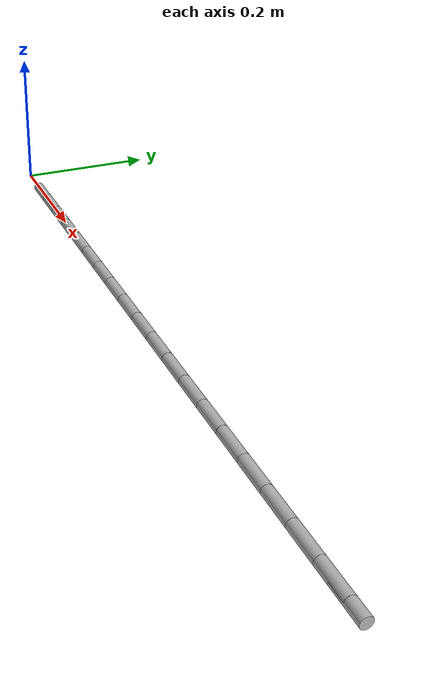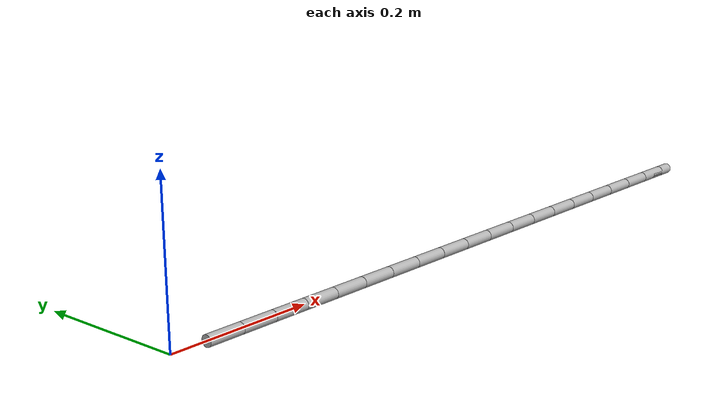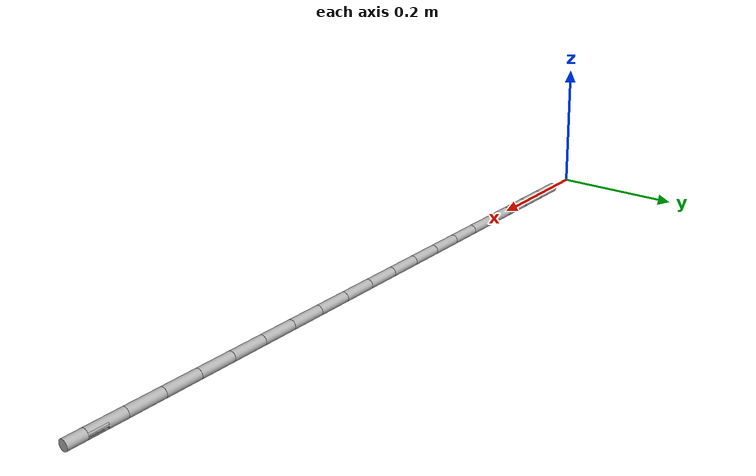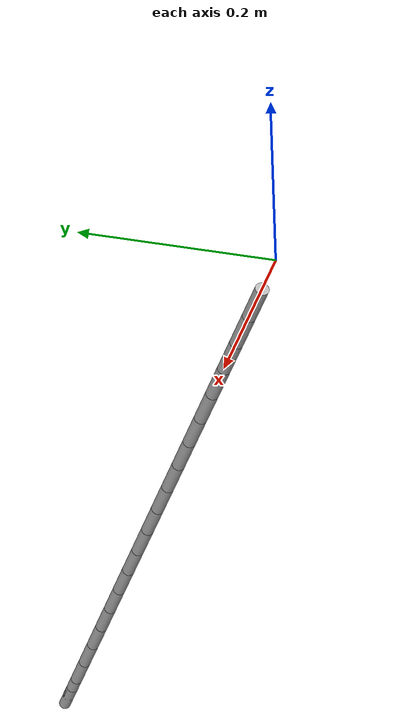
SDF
<?xml version='1.0'?>
<sdf version='1.7'>
  <model name='cable'>
    <link name='coupling'>
      <pose>1 -0 -0 0 -0 0</pose>
      <inertial>
        <pose>0 0 0 0 -0 0</pose>
        <mass>0.1</mass>
        <inertia>
          <ixx>0.01</ixx>
          <ixy>0</ixy>
          <ixz>0</ixz>
          <iyy>0.01</iyy>
          <iyz>0</iyz>
          <izz>0.01</izz>
        </inertia>
      </inertial>
      <velocity_decay/>
      <self_collide>0</self_collide>
      <kinematic>0</kinematic>
      <gravity>1</gravity>
      <enable_wind>0</enable_wind>
      <visual name='coupling_vis'>
        <pose>0 0 0 0 1.57079 0</pose>
        <geometry>
          <cylinder>
            <length>0.05</length>
            <radius>0.0075</radius>
          </cylinder>
        </geometry>
        <material>
          <shader type='pixel'/>
        </material>
        <transparency>0</transparency>
        <cast_shadows>1</cast_shadows>
      </visual>
      <collision name='coupling_collision'>
        <laser_retro>0</laser_retro>
        <max_contacts>10</max_contacts>
        <pose>0 0 0 0 1.57079 0</pose>
        <geometry>
          <cylinder>
            <radius>0.0075</radius>
            <length>0.05</length>
          </cylinder>
        </geometry>
        <surface>
          <friction>
            <ode>
              <mu>1</mu>
              <mu2>1</mu2>
              <fdir1>0 0 0</fdir1>
              <slip1>0</slip1>
              <slip2>0</slip2>
            </ode>
            <torsional>
              <coefficient>1</coefficient>
              <patch_radius>0</patch_radius>
              <surface_radius>0</surface_radius>
              <use_patch_radius>1</use_patch_radius>
              <ode>
                <slip>0</slip>
              </ode>
            </torsional>
          </friction>
          <bounce>
            <restitution_coefficient>0</restitution_coefficient>
            <threshold>1e+06</threshold>
          </bounce>
          <contact>
            <collide_without_contact>0</collide_without_contact>
            <collide_without_contact_bitmask>1</collide_without_contact_bitmask>
            <collide_bitmask>1</collide_bitmask>
            <ode>
              <soft_cfm>0</soft_cfm>
              <soft_erp>0.2</soft_erp>
              <kp>1e+13</kp>
              <kd>1</kd>
              <max_vel>0.01</max_vel>
              <min_depth>0</min_depth>
            </ode>
            <bullet>
              <split_impulse>1</split_impulse>
              <split_impulse_penetration_threshold>-0.01</split_impulse_penetration_threshold>
              <soft_cfm>0</soft_cfm>
              <soft_erp>0.2</soft_erp>
              <kp>1e+13</kp>
              <kd>1</kd>
            </bullet>
          </contact>
        </surface>
      </collision>
    </link>
    <link name='link_01'>
      <pose>0.05 -0 0 0 -0 0</pose>
      <inertial>
        <pose>0 0 0 0 -0 0</pose>
        <mass>0.1</mass>
        <inertia>
          <ixx>0.01</ixx>
          <ixy>0</ixy>
          <ixz>0</ixz>
          <iyy>0.01</iyy>
          <iyz>0</iyz>
          <izz>0.01</izz>
        </inertia>
      </inertial>
      <velocity_decay/>
      <self_collide>0</self_collide>
      <kinematic>0</kinematic>
      <gravity>1</gravity>
      <enable_wind>0</enable_wind>
      <visual name='link_01_vis'>
        <pose>0.025 0 0 0 1.57079 0</pose>
        <geometry>
          <cylinder>
            <length>0.05</length>
            <radius>0.0075</radius>
          </cylinder>
        </geometry>
        <material>
          <shader type='pixel'/>
        </material>
        <transparency>0</transparency>
        <cast_shadows>1</cast_shadows>
      </visual>
      <collision name='link_01_collision'>
        <laser_retro>0</laser_retro>
        <max_contacts>10</max_contacts>
        <pose>0.025 0 0 0 1.57079 0</pose>
        <geometry>
          <cylinder>
            <radius>0.0075</radius>
            <length>0.05</length>
          </cylinder>
        </geometry>
        <surface>
          <friction>
            <ode>
              <mu>1</mu>
              <mu2>1</mu2>
              <fdir1>0 0 0</fdir1>
              <slip1>0</slip1>
              <slip2>0</slip2>
            </ode>
            <torsional>
              <coefficient>1</coefficient>
              <patch_radius>0</patch_radius>
              <surface_radius>0</surface_radius>
              <use_patch_radius>1</use_patch_radius>
              <ode>
                <slip>0</slip>
              </ode>
            </torsional>
          </friction>
          <bounce>
            <restitution_coefficient>0</restitution_coefficient>
            <threshold>1e+06</threshold>
          </bounce>
          <contact>
            <collide_without_contact>0</collide_without_contact>
            <collide_without_contact_bitmask>1</collide_without_contact_bitmask>
            <collide_bitmask>1</collide_bitmask>
            <ode>
              <soft_cfm>0</soft_cfm>
              <soft_erp>0.2</soft_erp>
              <kp>1e+13</kp>
              <kd>1</kd>
              <max_vel>0.01</max_vel>
              <min_depth>0</min_depth>
            </ode>
            <bullet>
              <split_impulse>1</split_impulse>
              <split_impulse_penetration_threshold>-0.01</split_impulse_penetration_threshold>
              <soft_cfm>0</soft_cfm>
              <soft_erp>0.2</soft_erp>
              <kp>1e+13</kp>
              <kd>1</kd>
            </bullet>
          </contact>
        </surface>
      </collision>
    </link>
    <link name='link_02'>
      <pose>0.1 -0 0 0 -0 0</pose>
      <inertial>
        <pose>0 0 0 0 -0 0</pose>
        <mass>0.1</mass>
        <inertia>
          <ixx>0.01</ixx>
          <ixy>0</ixy>
          <ixz>0</ixz>
          <iyy>0.01</iyy>
          <iyz>0</iyz>
          <izz>0.01</izz>
        </inertia>
      </inertial>
      <velocity_decay/>
      <self_collide>0</self_collide>
      <kinematic>0</kinematic>
      <gravity>1</gravity>
      <enable_wind>0</enable_wind>
      <visual name='link_02_vis'>
        <pose>0.025 0 0 0 1.57079 0</pose>
        <geometry>
          <cylinder>
            <length>0.05</length>
            <radius>0.0075</radius>
          </cylinder>
        </geometry>
        <material>
          <shader type='pixel'/>
        </material>
        <transparency>0</transparency>
        <cast_shadows>1</cast_shadows>
      </visual>
      <collision name='link_02_collision'>
        <laser_retro>0</laser_retro>
        <max_contacts>10</max_contacts>
        <pose>0.025 0 0 0 1.57079 0</pose>
        <geometry>
          <cylinder>
            <radius>0.0075</radius>
            <length>0.05</length>
          </cylinder>
        </geometry>
        <surface>
          <friction>
            <ode>
              <mu>1</mu>
              <mu2>1</mu2>
              <fdir1>0 0 0</fdir1>
              <slip1>0</slip1>
              <slip2>0</slip2>
            </ode>
            <torsional>
              <coefficient>1</coefficient>
              <patch_radius>0</patch_radius>
              <surface_radius>0</surface_radius>
              <use_patch_radius>1</use_patch_radius>
              <ode>
                <slip>0</slip>
              </ode>
            </torsional>
          </friction>
          <bounce>
            <restitution_coefficient>0</restitution_coefficient>
            <threshold>1e+06</threshold>
          </bounce>
          <contact>
            <collide_without_contact>0</collide_without_contact>
            <collide_without_contact_bitmask>1</collide_without_contact_bitmask>
            <collide_bitmask>1</collide_bitmask>
            <ode>
              <soft_cfm>0</soft_cfm>
              <soft_erp>0.2</soft_erp>
              <kp>1e+13</kp>
              <kd>1</kd>
              <max_vel>0.01</max_vel>
              <min_depth>0</min_depth>
            </ode>
            <bullet>
              <split_impulse>1</split_impulse>
              <split_impulse_penetration_threshold>-0.01</split_impulse_penetration_threshold>
              <soft_cfm>0</soft_cfm>
              <soft_erp>0.2</soft_erp>
              <kp>1e+13</kp>
              <kd>1</kd>
            </bullet>
          </contact>
        </surface>
      </collision>
    </link>
    <link name='link_03'>
      <pose>0.15 -0 0 0 -0 0</pose>
      <inertial>
        <pose>0 0 0 0 -0 0</pose>
        <mass>0.1</mass>
        <inertia>
          <ixx>0.01</ixx>
          <ixy>0</ixy>
          <ixz>0</ixz>
          <iyy>0.01</iyy>
          <iyz>0</iyz>
          <izz>0.01</izz>
        </inertia>
      </inertial>
      <velocity_decay/>
      <self_collide>0</self_collide>
      <kinematic>0</kinematic>
      <gravity>1</gravity>
      <enable_wind>0</enable_wind>
      <visual name='link_03_vis'>
        <pose>0.025 0 0 0 1.57079 0</pose>
        <geometry>
          <cylinder>
            <length>0.05</length>
            <radius>0.0075</radius>
          </cylinder>
        </geometry>
        <material>
          <shader type='pixel'/>
        </material>
        <transparency>0</transparency>
        <cast_shadows>1</cast_shadows>
      </visual>
      <collision name='link_03_collision'>
        <laser_retro>0</laser_retro>
        <max_contacts>10</max_contacts>
        <pose>0.025 0 0 0 1.57079 0</pose>
        <geometry>
          <cylinder>
            <radius>0.0075</radius>
            <length>0.05</length>
          </cylinder>
        </geometry>
        <surface>
          <friction>
            <ode>
              <mu>1</mu>
              <mu2>1</mu2>
              <fdir1>0 0 0</fdir1>
              <slip1>0</slip1>
              <slip2>0</slip2>
            </ode>
            <torsional>
              <coefficient>1</coefficient>
              <patch_radius>0</patch_radius>
              <surface_radius>0</surface_radius>
              <use_patch_radius>1</use_patch_radius>
              <ode>
                <slip>0</slip>
              </ode>
            </torsional>
          </friction>
          <bounce>
            <restitution_coefficient>0</restitution_coefficient>
            <threshold>1e+06</threshold>
          </bounce>
          <contact>
            <collide_without_contact>0</collide_without_contact>
            <collide_without_contact_bitmask>1</collide_without_contact_bitmask>
            <collide_bitmask>1</collide_bitmask>
            <ode>
              <soft_cfm>0</soft_cfm>
              <soft_erp>0.2</soft_erp>
              <kp>1e+13</kp>
              <kd>1</kd>
              <max_vel>0.01</max_vel>
              <min_depth>0</min_depth>
            </ode>
            <bullet>
              <split_impulse>1</split_impulse>
              <split_impulse_penetration_threshold>-0.01</split_impulse_penetration_threshold>
              <soft_cfm>0</soft_cfm>
              <soft_erp>0.2</soft_erp>
              <kp>1e+13</kp>
              <kd>1</kd>
            </bullet>
          </contact>
        </surface>
      </collision>
    </link>
    <link name='link_04'>
      <pose>0.2 -0 0 0 -0 0</pose>
      <inertial>
        <pose>0 0 0 0 -0 0</pose>
        <mass>0.1</mass>
        <inertia>
          <ixx>0.01</ixx>
          <ixy>0</ixy>
          <ixz>0</ixz>
          <iyy>0.01</iyy>
          <iyz>0</iyz>
          <izz>0.01</izz>
        </inertia>
      </inertial>
      <velocity_decay/>
      <self_collide>0</self_collide>
      <kinematic>0</kinematic>
      <gravity>1</gravity>
      <enable_wind>0</enable_wind>
      <visual name='link_04_vis'>
        <pose>0.025 0 0 0 1.57079 0</pose>
        <geometry>
          <cylinder>
            <length>0.05</length>
            <radius>0.0075</radius>
          </cylinder>
        </geometry>
        <material>
          <shader type='pixel'/>
        </material>
        <transparency>0</transparency>
        <cast_shadows>1</cast_shadows>
      </visual>
      <collision name='link_04_collision'>
        <laser_retro>0</laser_retro>
        <max_contacts>10</max_contacts>
        <pose>0.025 0 0 0 1.57079 0</pose>
        <geometry>
          <cylinder>
            <radius>0.0075</radius>
            <length>0.05</length>
          </cylinder>
        </geometry>
        <surface>
          <friction>
            <ode>
              <mu>1</mu>
              <mu2>1</mu2>
              <fdir1>0 0 0</fdir1>
              <slip1>0</slip1>
              <slip2>0</slip2>
            </ode>
            <torsional>
              <coefficient>1</coefficient>
              <patch_radius>0</patch_radius>
              <surface_radius>0</surface_radius>
              <use_patch_radius>1</use_patch_radius>
              <ode>
                <slip>0</slip>
              </ode>
            </torsional>
          </friction>
          <bounce>
            <restitution_coefficient>0</restitution_coefficient>
            <threshold>1e+06</threshold>
          </bounce>
          <contact>
            <collide_without_contact>0</collide_without_contact>
            <collide_without_contact_bitmask>1</collide_without_contact_bitmask>
            <collide_bitmask>1</collide_bitmask>
            <ode>
              <soft_cfm>0</soft_cfm>
              <soft_erp>0.2</soft_erp>
              <kp>1e+13</kp>
              <kd>1</kd>
              <max_vel>0.01</max_vel>
              <min_depth>0</min_depth>
            </ode>
            <bullet>
              <split_impulse>1</split_impulse>
              <split_impulse_penetration_threshold>-0.01</split_impulse_penetration_threshold>
              <soft_cfm>0</soft_cfm>
              <soft_erp>0.2</soft_erp>
              <kp>1e+13</kp>
              <kd>1</kd>
            </bullet>
          </contact>
        </surface>
      </collision>
    </link>
    <link name='link_05'>
      <pose>0.25 -0 0 0 -0 0</pose>
      <inertial>
        <pose>0 0 0 0 -0 0</pose>
        <mass>0.1</mass>
        <inertia>
          <ixx>0.01</ixx>
          <ixy>0</ixy>
          <ixz>0</ixz>
          <iyy>0.01</iyy>
          <iyz>0</iyz>
          <izz>0.01</izz>
        </inertia>
      </inertial>
      <velocity_decay/>
      <self_collide>0</self_collide>
      <kinematic>0</kinematic>
      <gravity>1</gravity>
      <enable_wind>0</enable_wind>
      <visual name='link_05_vis'>
        <pose>0.025 0 0 0 1.57079 0</pose>
        <geometry>
          <cylinder>
            <length>0.05</length>
            <radius>0.0075</radius>
          </cylinder>
        </geometry>
        <material>
          <shader type='pixel'/>
        </material>
        <transparency>0</transparency>
        <cast_shadows>1</cast_shadows>
      </visual>
      <collision name='link_05_collision'>
        <laser_retro>0</laser_retro>
        <max_contacts>10</max_contacts>
        <pose>0.025 0 0 0 1.57079 0</pose>
        <geometry>
          <cylinder>
            <radius>0.0075</radius>
            <length>0.05</length>
          </cylinder>
        </geometry>
        <surface>
          <friction>
            <ode>
              <mu>1</mu>
              <mu2>1</mu2>
              <fdir1>0 0 0</fdir1>
              <slip1>0</slip1>
              <slip2>0</slip2>
            </ode>
            <torsional>
              <coefficient>1</coefficient>
              <patch_radius>0</patch_radius>
              <surface_radius>0</surface_radius>
              <use_patch_radius>1</use_patch_radius>
              <ode>
                <slip>0</slip>
              </ode>
            </torsional>
          </friction>
          <bounce>
            <restitution_coefficient>0</restitution_coefficient>
            <threshold>1e+06</threshold>
          </bounce>
          <contact>
            <collide_without_contact>0</collide_without_contact>
            <collide_without_contact_bitmask>1</collide_without_contact_bitmask>
            <collide_bitmask>1</collide_bitmask>
            <ode>
              <soft_cfm>0</soft_cfm>
              <soft_erp>0.2</soft_erp>
              <kp>1e+13</kp>
              <kd>1</kd>
              <max_vel>0.01</max_vel>
              <min_depth>0</min_depth>
            </ode>
            <bullet>
              <split_impulse>1</split_impulse>
              <split_impulse_penetration_threshold>-0.01</split_impulse_penetration_threshold>
              <soft_cfm>0</soft_cfm>
              <soft_erp>0.2</soft_erp>
              <kp>1e+13</kp>
              <kd>1</kd>
            </bullet>
          </contact>
        </surface>
      </collision>
    </link>
    <link name='link_06'>
      <pose>0.3 -0 0 0 -0 0</pose>
      <inertial>
        <pose>0 0 0 0 -0 0</pose>
        <mass>0.1</mass>
        <inertia>
          <ixx>0.01</ixx>
          <ixy>0</ixy>
          <ixz>0</ixz>
          <iyy>0.01</iyy>
          <iyz>0</iyz>
          <izz>0.01</izz>
        </inertia>
      </inertial>
      <velocity_decay/>
      <self_collide>0</self_collide>
      <kinematic>0</kinematic>
      <gravity>1</gravity>
      <enable_wind>0</enable_wind>
      <visual name='link_06_vis'>
        <pose>0.025 0 0 0 1.57079 0</pose>
        <geometry>
          <cylinder>
            <length>0.05</length>
            <radius>0.0075</radius>
          </cylinder>
        </geometry>
        <material>
          <shader type='pixel'/>
        </material>
        <transparency>0</transparency>
        <cast_shadows>1</cast_shadows>
      </visual>
      <collision name='link_06_collision'>
        <laser_retro>0</laser_retro>
        <max_contacts>10</max_contacts>
        <pose>0.025 0 0 0 1.57079 0</pose>
        <geometry>
          <cylinder>
            <radius>0.0075</radius>
            <length>0.05</length>
          </cylinder>
        </geometry>
        <surface>
          <friction>
            <ode>
              <mu>1</mu>
              <mu2>1</mu2>
              <fdir1>0 0 0</fdir1>
              <slip1>0</slip1>
              <slip2>0</slip2>
            </ode>
            <torsional>
              <coefficient>1</coefficient>
              <patch_radius>0</patch_radius>
              <surface_radius>0</surface_radius>
              <use_patch_radius>1</use_patch_radius>
              <ode>
                <slip>0</slip>
              </ode>
            </torsional>
          </friction>
          <bounce>
            <restitution_coefficient>0</restitution_coefficient>
            <threshold>1e+06</threshold>
          </bounce>
          <contact>
            <collide_without_contact>0</collide_without_contact>
            <collide_without_contact_bitmask>1</collide_without_contact_bitmask>
            <collide_bitmask>1</collide_bitmask>
            <ode>
              <soft_cfm>0</soft_cfm>
              <soft_erp>0.2</soft_erp>
              <kp>1e+13</kp>
              <kd>1</kd>
              <max_vel>0.01</max_vel>
              <min_depth>0</min_depth>
            </ode>
            <bullet>
              <split_impulse>1</split_impulse>
              <split_impulse_penetration_threshold>-0.01</split_impulse_penetration_threshold>
              <soft_cfm>0</soft_cfm>
              <soft_erp>0.2</soft_erp>
              <kp>1e+13</kp>
              <kd>1</kd>
            </bullet>
          </contact>
        </surface>
      </collision>
    </link>
    <link name='link_07'>
      <pose>0.35 -0 0 0 -0 0</pose>
      <inertial>
        <pose>0 0 0 0 -0 0</pose>
        <mass>0.1</mass>
        <inertia>
          <ixx>0.01</ixx>
          <ixy>0</ixy>
          <ixz>0</ixz>
          <iyy>0.01</iyy>
          <iyz>0</iyz>
          <izz>0.01</izz>
        </inertia>
      </inertial>
      <velocity_decay/>
      <self_collide>0</self_collide>
      <kinematic>0</kinematic>
      <gravity>1</gravity>
      <enable_wind>0</enable_wind>
      <visual name='link_07_vis'>
        <pose>0.025 0 0 0 1.57079 0</pose>
        <geometry>
          <cylinder>
            <length>0.05</length>
            <radius>0.0075</radius>
          </cylinder>
        </geometry>
        <material>
          <shader type='pixel'/>
        </material>
        <transparency>0</transparency>
        <cast_shadows>1</cast_shadows>
      </visual>
      <collision name='link_07_collision'>
        <laser_retro>0</laser_retro>
        <max_contacts>10</max_contacts>
        <pose>0.025 0 0 0 1.57079 0</pose>
        <geometry>
          <cylinder>
            <radius>0.0075</radius>
            <length>0.05</length>
          </cylinder>
        </geometry>
        <surface>
          <friction>
            <ode>
              <mu>1</mu>
              <mu2>1</mu2>
              <fdir1>0 0 0</fdir1>
              <slip1>0</slip1>
              <slip2>0</slip2>
            </ode>
            <torsional>
              <coefficient>1</coefficient>
              <patch_radius>0</patch_radius>
              <surface_radius>0</surface_radius>
              <use_patch_radius>1</use_patch_radius>
              <ode>
                <slip>0</slip>
              </ode>
            </torsional>
          </friction>
          <bounce>
            <restitution_coefficient>0</restitution_coefficient>
            <threshold>1e+06</threshold>
          </bounce>
          <contact>
            <collide_without_contact>0</collide_without_contact>
            <collide_without_contact_bitmask>1</collide_without_contact_bitmask>
            <collide_bitmask>1</collide_bitmask>
            <ode>
              <soft_cfm>0</soft_cfm>
              <soft_erp>0.2</soft_erp>
              <kp>1e+13</kp>
              <kd>1</kd>
              <max_vel>0.01</max_vel>
              <min_depth>0</min_depth>
            </ode>
            <bullet>
              <split_impulse>1</split_impulse>
              <split_impulse_penetration_threshold>-0.01</split_impulse_penetration_threshold>
              <soft_cfm>0</soft_cfm>
              <soft_erp>0.2</soft_erp>
              <kp>1e+13</kp>
              <kd>1</kd>
            </bullet>
          </contact>
        </surface>
      </collision>
    </link>
    <link name='link_08'>
      <pose>0.4 -0 0 0 -0 0</pose>
      <inertial>
        <pose>0 0 0 0 -0 0</pose>
        <mass>0.1</mass>
        <inertia>
          <ixx>0.01</ixx>
          <ixy>0</ixy>
          <ixz>0</ixz>
          <iyy>0.01</iyy>
          <iyz>0</iyz>
          <izz>0.01</izz>
        </inertia>
      </inertial>
      <velocity_decay/>
      <self_collide>0</self_collide>
      <kinematic>0</kinematic>
      <gravity>1</gravity>
      <enable_wind>0</enable_wind>
      <visual name='link_08_vis'>
        <pose>0.025 0 0 0 1.57079 0</pose>
        <geometry>
          <cylinder>
            <length>0.05</length>
            <radius>0.0075</radius>
          </cylinder>
        </geometry>
        <material>
          <shader type='pixel'/>
        </material>
        <transparency>0</transparency>
        <cast_shadows>1</cast_shadows>
      </visual>
      <collision name='link_08_collision'>
        <laser_retro>0</laser_retro>
        <max_contacts>10</max_contacts>
        <pose>0.025 0 0 0 1.57079 0</pose>
        <geometry>
          <cylinder>
            <radius>0.0075</radius>
            <length>0.05</length>
          </cylinder>
        </geometry>
        <surface>
          <friction>
            <ode>
              <mu>1</mu>
              <mu2>1</mu2>
              <fdir1>0 0 0</fdir1>
              <slip1>0</slip1>
              <slip2>0</slip2>
            </ode>
            <torsional>
              <coefficient>1</coefficient>
              <patch_radius>0</patch_radius>
              <surface_radius>0</surface_radius>
              <use_patch_radius>1</use_patch_radius>
              <ode>
                <slip>0</slip>
              </ode>
            </torsional>
          </friction>
          <bounce>
            <restitution_coefficient>0</restitution_coefficient>
            <threshold>1e+06</threshold>
          </bounce>
          <contact>
            <collide_without_contact>0</collide_without_contact>
            <collide_without_contact_bitmask>1</collide_without_contact_bitmask>
            <collide_bitmask>1</collide_bitmask>
            <ode>
              <soft_cfm>0</soft_cfm>
              <soft_erp>0.2</soft_erp>
              <kp>1e+13</kp>
              <kd>1</kd>
              <max_vel>0.01</max_vel>
              <min_depth>0</min_depth>
            </ode>
            <bullet>
              <split_impulse>1</split_impulse>
              <split_impulse_penetration_threshold>-0.01</split_impulse_penetration_threshold>
              <soft_cfm>0</soft_cfm>
              <soft_erp>0.2</soft_erp>
              <kp>1e+13</kp>
              <kd>1</kd>
            </bullet>
          </contact>
        </surface>
      </collision>
    </link>
    <link name='link_09'>
      <pose>0.45 -0 0 0 -0 0</pose>
      <inertial>
        <pose>0 0 0 0 -0 0</pose>
        <mass>0.1</mass>
        <inertia>
          <ixx>0.01</ixx>
          <ixy>0</ixy>
          <ixz>0</ixz>
          <iyy>0.01</iyy>
          <iyz>0</iyz>
          <izz>0.01</izz>
        </inertia>
      </inertial>
      <velocity_decay/>
      <self_collide>0</self_collide>
      <kinematic>0</kinematic>
      <gravity>1</gravity>
      <enable_wind>0</enable_wind>
      <visual name='link_09_vis'>
        <pose>0.025 0 0 0 1.57079 0</pose>
        <geometry>
          <cylinder>
            <length>0.05</length>
            <radius>0.0075</radius>
          </cylinder>
        </geometry>
        <material>
          <shader type='pixel'/>
        </material>
        <transparency>0</transparency>
        <cast_shadows>1</cast_shadows>
      </visual>
      <collision name='link_09_collision'>
        <laser_retro>0</laser_retro>
        <max_contacts>10</max_contacts>
        <pose>0.025 0 0 0 1.57079 0</pose>
        <geometry>
          <cylinder>
            <radius>0.0075</radius>
            <length>0.05</length>
          </cylinder>
        </geometry>
        <surface>
          <friction>
            <ode>
              <mu>1</mu>
              <mu2>1</mu2>
              <fdir1>0 0 0</fdir1>
              <slip1>0</slip1>
              <slip2>0</slip2>
            </ode>
            <torsional>
              <coefficient>1</coefficient>
              <patch_radius>0</patch_radius>
              <surface_radius>0</surface_radius>
              <use_patch_radius>1</use_patch_radius>
              <ode>
                <slip>0</slip>
              </ode>
            </torsional>
          </friction>
          <bounce>
            <restitution_coefficient>0</restitution_coefficient>
            <threshold>1e+06</threshold>
          </bounce>
          <contact>
            <collide_without_contact>0</collide_without_contact>
            <collide_without_contact_bitmask>1</collide_without_contact_bitmask>
            <collide_bitmask>1</collide_bitmask>
            <ode>
              <soft_cfm>0</soft_cfm>
              <soft_erp>0.2</soft_erp>
              <kp>1e+13</kp>
              <kd>1</kd>
              <max_vel>0.01</max_vel>
              <min_depth>0</min_depth>
            </ode>
            <bullet>
              <split_impulse>1</split_impulse>
              <split_impulse_penetration_threshold>-0.01</split_impulse_penetration_threshold>
              <soft_cfm>0</soft_cfm>
              <soft_erp>0.2</soft_erp>
              <kp>1e+13</kp>
              <kd>1</kd>
            </bullet>
          </contact>
        </surface>
      </collision>
    </link>
    <link name='link_10'>
      <pose>0.5 -0 0 0 -0 0</pose>
      <inertial>
        <pose>0 0 0 0 -0 0</pose>
        <mass>0.1</mass>
        <inertia>
          <ixx>0.01</ixx>
          <ixy>0</ixy>
          <ixz>0</ixz>
          <iyy>0.01</iyy>
          <iyz>0</iyz>
          <izz>0.01</izz>
        </inertia>
      </inertial>
      <velocity_decay/>
      <self_collide>0</self_collide>
      <kinematic>0</kinematic>
      <gravity>1</gravity>
      <enable_wind>0</enable_wind>
      <visual name='link_10_vis'>
        <pose>0.025 0 0 0 1.57079 0</pose>
        <geometry>
          <cylinder>
            <length>0.05</length>
            <radius>0.0075</radius>
          </cylinder>
        </geometry>
        <material>
          <shader type='pixel'/>
        </material>
        <transparency>0</transparency>
        <cast_shadows>1</cast_shadows>
      </visual>
      <collision name='link_10_collision'>
        <laser_retro>0</laser_retro>
        <max_contacts>10</max_contacts>
        <pose>0.025 0 0 0 1.57079 0</pose>
        <geometry>
          <cylinder>
            <radius>0.0075</radius>
            <length>0.05</length>
          </cylinder>
        </geometry>
        <surface>
          <friction>
            <ode>
              <mu>1</mu>
              <mu2>1</mu2>
              <fdir1>0 0 0</fdir1>
              <slip1>0</slip1>
              <slip2>0</slip2>
            </ode>
            <torsional>
              <coefficient>1</coefficient>
              <patch_radius>0</patch_radius>
              <surface_radius>0</surface_radius>
              <use_patch_radius>1</use_patch_radius>
              <ode>
                <slip>0</slip>
              </ode>
            </torsional>
          </friction>
          <bounce>
            <restitution_coefficient>0</restitution_coefficient>
            <threshold>1e+06</threshold>
          </bounce>
          <contact>
            <collide_without_contact>0</collide_without_contact>
            <collide_without_contact_bitmask>1</collide_without_contact_bitmask>
            <collide_bitmask>1</collide_bitmask>
            <ode>
              <soft_cfm>0</soft_cfm>
              <soft_erp>0.2</soft_erp>
              <kp>1e+13</kp>
              <kd>1</kd>
              <max_vel>0.01</max_vel>
              <min_depth>0</min_depth>
            </ode>
            <bullet>
              <split_impulse>1</split_impulse>
              <split_impulse_penetration_threshold>-0.01</split_impulse_penetration_threshold>
              <soft_cfm>0</soft_cfm>
              <soft_erp>0.2</soft_erp>
              <kp>1e+13</kp>
              <kd>1</kd>
            </bullet>
          </contact>
        </surface>
      </collision>
    </link>
    <link name='link_11'>
      <pose>0.55 -0 0 0 -0 0</pose>
      <inertial>
        <pose>0 0 0 0 -0 0</pose>
        <mass>0.1</mass>
        <inertia>
          <ixx>0.01</ixx>
          <ixy>0</ixy>
          <ixz>0</ixz>
          <iyy>0.01</iyy>
          <iyz>0</iyz>
          <izz>0.01</izz>
        </inertia>
      </inertial>
      <velocity_decay/>
      <self_collide>0</self_collide>
      <kinematic>0</kinematic>
      <gravity>1</gravity>
      <enable_wind>0</enable_wind>
      <visual name='link_11_vis'>
        <pose>0.025 0 0 0 1.57079 0</pose>
        <geometry>
          <cylinder>
            <length>0.05</length>
            <radius>0.0075</radius>
          </cylinder>
        </geometry>
        <material>
          <shader type='pixel'/>
        </material>
        <transparency>0</transparency>
        <cast_shadows>1</cast_shadows>
      </visual>
      <collision name='link_11_collision'>
        <laser_retro>0</laser_retro>
        <max_contacts>10</max_contacts>
        <pose>0.025 0 0 0 1.57079 0</pose>
        <geometry>
          <cylinder>
            <radius>0.0075</radius>
            <length>0.05</length>
          </cylinder>
        </geometry>
        <surface>
          <friction>
            <ode>
              <mu>1</mu>
              <mu2>1</mu2>
              <fdir1>0 0 0</fdir1>
              <slip1>0</slip1>
              <slip2>0</slip2>
            </ode>
            <torsional>
              <coefficient>1</coefficient>
              <patch_radius>0</patch_radius>
              <surface_radius>0</surface_radius>
              <use_patch_radius>1</use_patch_radius>
              <ode>
                <slip>0</slip>
              </ode>
            </torsional>
          </friction>
          <bounce>
            <restitution_coefficient>0</restitution_coefficient>
            <threshold>1e+06</threshold>
          </bounce>
          <contact>
            <collide_without_contact>0</collide_without_contact>
            <collide_without_contact_bitmask>1</collide_without_contact_bitmask>
            <collide_bitmask>1</collide_bitmask>
            <ode>
              <soft_cfm>0</soft_cfm>
              <soft_erp>0.2</soft_erp>
              <kp>1e+13</kp>
              <kd>1</kd>
              <max_vel>0.01</max_vel>
              <min_depth>0</min_depth>
            </ode>
            <bullet>
              <split_impulse>1</split_impulse>
              <split_impulse_penetration_threshold>-0.01</split_impulse_penetration_threshold>
              <soft_cfm>0</soft_cfm>
              <soft_erp>0.2</soft_erp>
              <kp>1e+13</kp>
              <kd>1</kd>
            </bullet>
          </contact>
        </surface>
      </collision>
    </link>
    <link name='link_12'>
      <pose>0.6 -0 -0 0 -0 0</pose>
      <inertial>
        <pose>0 0 0 0 -0 0</pose>
        <mass>0.1</mass>
        <inertia>
          <ixx>0.01</ixx>
          <ixy>0</ixy>
          <ixz>0</ixz>
          <iyy>0.01</iyy>
          <iyz>0</iyz>
          <izz>0.01</izz>
        </inertia>
      </inertial>
      <velocity_decay/>
      <self_collide>0</self_collide>
      <kinematic>0</kinematic>
      <gravity>1</gravity>
      <enable_wind>0</enable_wind>
      <visual name='link_12_vis'>
        <pose>0.025 0 0 0 1.57079 0</pose>
        <geometry>
          <cylinder>
            <length>0.05</length>
            <radius>0.0075</radius>
          </cylinder>
        </geometry>
        <material>
          <shader type='pixel'/>
        </material>
        <transparency>0</transparency>
        <cast_shadows>1</cast_shadows>
      </visual>
      <collision name='link_12_collision'>
        <laser_retro>0</laser_retro>
        <max_contacts>10</max_contacts>
        <pose>0.025 0 0 0 1.57079 0</pose>
        <geometry>
          <cylinder>
            <radius>0.0075</radius>
            <length>0.05</length>
          </cylinder>
        </geometry>
        <surface>
          <friction>
            <ode>
              <mu>1</mu>
              <mu2>1</mu2>
              <fdir1>0 0 0</fdir1>
              <slip1>0</slip1>
              <slip2>0</slip2>
            </ode>
            <torsional>
              <coefficient>1</coefficient>
              <patch_radius>0</patch_radius>
              <surface_radius>0</surface_radius>
              <use_patch_radius>1</use_patch_radius>
              <ode>
                <slip>0</slip>
              </ode>
            </torsional>
          </friction>
          <bounce>
            <restitution_coefficient>0</restitution_coefficient>
            <threshold>1e+06</threshold>
          </bounce>
          <contact>
            <collide_without_contact>0</collide_without_contact>
            <collide_without_contact_bitmask>1</collide_without_contact_bitmask>
            <collide_bitmask>1</collide_bitmask>
            <ode>
              <soft_cfm>0</soft_cfm>
              <soft_erp>0.2</soft_erp>
              <kp>1e+13</kp>
              <kd>1</kd>
              <max_vel>0.01</max_vel>
              <min_depth>0</min_depth>
            </ode>
            <bullet>
              <split_impulse>1</split_impulse>
              <split_impulse_penetration_threshold>-0.01</split_impulse_penetration_threshold>
              <soft_cfm>0</soft_cfm>
              <soft_erp>0.2</soft_erp>
              <kp>1e+13</kp>
              <kd>1</kd>
            </bullet>
          </contact>
        </surface>
      </collision>
    </link>
    <link name='link_13'>
      <pose>0.65 -0 -0 0 -0 0</pose>
      <inertial>
        <pose>0 0 0 0 -0 0</pose>
        <mass>0.1</mass>
        <inertia>
          <ixx>0.01</ixx>
          <ixy>0</ixy>
          <ixz>0</ixz>
          <iyy>0.01</iyy>
          <iyz>0</iyz>
          <izz>0.01</izz>
        </inertia>
      </inertial>
      <velocity_decay/>
      <self_collide>0</self_collide>
      <kinematic>0</kinematic>
      <gravity>1</gravity>
      <enable_wind>0</enable_wind>
      <visual name='link_13_vis'>
        <pose>0.025 0 0 0 1.57079 0</pose>
        <geometry>
          <cylinder>
            <length>0.05</length>
            <radius>0.0075</radius>
          </cylinder>
        </geometry>
        <material>
          <shader type='pixel'/>
        </material>
        <transparency>0</transparency>
        <cast_shadows>1</cast_shadows>
      </visual>
      <collision name='link_13_collision'>
        <laser_retro>0</laser_retro>
        <max_contacts>10</max_contacts>
        <pose>0.025 0 0 0 1.57079 0</pose>
        <geometry>
          <cylinder>
            <radius>0.0075</radius>
            <length>0.05</length>
          </cylinder>
        </geometry>
        <surface>
          <friction>
            <ode>
              <mu>1</mu>
              <mu2>1</mu2>
              <fdir1>0 0 0</fdir1>
              <slip1>0</slip1>
              <slip2>0</slip2>
            </ode>
            <torsional>
              <coefficient>1</coefficient>
              <patch_radius>0</patch_radius>
              <surface_radius>0</surface_radius>
              <use_patch_radius>1</use_patch_radius>
              <ode>
                <slip>0</slip>
              </ode>
            </torsional>
          </friction>
          <bounce>
            <restitution_coefficient>0</restitution_coefficient>
            <threshold>1e+06</threshold>
          </bounce>
          <contact>
            <collide_without_contact>0</collide_without_contact>
            <collide_without_contact_bitmask>1</collide_without_contact_bitmask>
            <collide_bitmask>1</collide_bitmask>
            <ode>
              <soft_cfm>0</soft_cfm>
              <soft_erp>0.2</soft_erp>
              <kp>1e+13</kp>
              <kd>1</kd>
              <max_vel>0.01</max_vel>
              <min_depth>0</min_depth>
            </ode>
            <bullet>
              <split_impulse>1</split_impulse>
              <split_impulse_penetration_threshold>-0.01</split_impulse_penetration_threshold>
              <soft_cfm>0</soft_cfm>
              <soft_erp>0.2</soft_erp>
              <kp>1e+13</kp>
              <kd>1</kd>
            </bullet>
          </contact>
        </surface>
      </collision>
    </link>
    <link name='link_14'>
      <pose>0.7 -0 -0 0 -0 0</pose>
      <inertial>
        <pose>0 0 0 0 -0 0</pose>
        <mass>0.1</mass>
        <inertia>
          <ixx>0.01</ixx>
          <ixy>0</ixy>
          <ixz>0</ixz>
          <iyy>0.01</iyy>
          <iyz>0</iyz>
          <izz>0.01</izz>
        </inertia>
      </inertial>
      <velocity_decay/>
      <self_collide>0</self_collide>
      <kinematic>0</kinematic>
      <gravity>1</gravity>
      <enable_wind>0</enable_wind>
      <visual name='link_14_vis'>
        <pose>0.025 0 0 0 1.57079 0</pose>
        <geometry>
          <cylinder>
            <length>0.05</length>
            <radius>0.0075</radius>
          </cylinder>
        </geometry>
        <material>
          <shader type='pixel'/>
        </material>
        <transparency>0</transparency>
        <cast_shadows>1</cast_shadows>
      </visual>
      <collision name='link_14_collision'>
        <laser_retro>0</laser_retro>
        <max_contacts>10</max_contacts>
        <pose>0.025 0 0 0 1.57079 0</pose>
        <geometry>
          <cylinder>
            <radius>0.0075</radius>
            <length>0.05</length>
          </cylinder>
        </geometry>
        <surface>
          <friction>
            <ode>
              <mu>1</mu>
              <mu2>1</mu2>
              <fdir1>0 0 0</fdir1>
              <slip1>0</slip1>
              <slip2>0</slip2>
            </ode>
            <torsional>
              <coefficient>1</coefficient>
              <patch_radius>0</patch_radius>
              <surface_radius>0</surface_radius>
              <use_patch_radius>1</use_patch_radius>
              <ode>
                <slip>0</slip>
              </ode>
            </torsional>
          </friction>
          <bounce>
            <restitution_coefficient>0</restitution_coefficient>
            <threshold>1e+06</threshold>
          </bounce>
          <contact>
            <collide_without_contact>0</collide_without_contact>
            <collide_without_contact_bitmask>1</collide_without_contact_bitmask>
            <collide_bitmask>1</collide_bitmask>
            <ode>
              <soft_cfm>0</soft_cfm>
              <soft_erp>0.2</soft_erp>
              <kp>1e+13</kp>
              <kd>1</kd>
              <max_vel>0.01</max_vel>
              <min_depth>0</min_depth>
            </ode>
            <bullet>
              <split_impulse>1</split_impulse>
              <split_impulse_penetration_threshold>-0.01</split_impulse_penetration_threshold>
              <soft_cfm>0</soft_cfm>
              <soft_erp>0.2</soft_erp>
              <kp>1e+13</kp>
              <kd>1</kd>
            </bullet>
          </contact>
        </surface>
      </collision>
    </link>
    <link name='link_15'>
      <pose>0.75 -0 -0 0 -0 0</pose>
      <inertial>
        <pose>0 0 0 0 -0 0</pose>
        <mass>0.1</mass>
        <inertia>
          <ixx>0.01</ixx>
          <ixy>0</ixy>
          <ixz>0</ixz>
          <iyy>0.01</iyy>
          <iyz>0</iyz>
          <izz>0.01</izz>
        </inertia>
      </inertial>
      <velocity_decay/>
      <self_collide>0</self_collide>
      <kinematic>0</kinematic>
      <gravity>1</gravity>
      <enable_wind>0</enable_wind>
      <visual name='link_15_vis'>
        <pose>0.025 0 0 0 1.57079 0</pose>
        <geometry>
          <cylinder>
            <length>0.05</length>
            <radius>0.0075</radius>
          </cylinder>
        </geometry>
        <material>
          <shader type='pixel'/>
        </material>
        <transparency>0</transparency>
        <cast_shadows>1</cast_shadows>
      </visual>
      <collision name='link_15_collision'>
        <laser_retro>0</laser_retro>
        <max_contacts>10</max_contacts>
        <pose>0.025 0 0 0 1.57079 0</pose>
        <geometry>
          <cylinder>
            <radius>0.0075</radius>
            <length>0.05</length>
          </cylinder>
        </geometry>
        <surface>
          <friction>
            <ode>
              <mu>1</mu>
              <mu2>1</mu2>
              <fdir1>0 0 0</fdir1>
              <slip1>0</slip1>
              <slip2>0</slip2>
            </ode>
            <torsional>
              <coefficient>1</coefficient>
              <patch_radius>0</patch_radius>
              <surface_radius>0</surface_radius>
              <use_patch_radius>1</use_patch_radius>
              <ode>
                <slip>0</slip>
              </ode>
            </torsional>
          </friction>
          <bounce>
            <restitution_coefficient>0</restitution_coefficient>
            <threshold>1e+06</threshold>
          </bounce>
          <contact>
            <collide_without_contact>0</collide_without_contact>
            <collide_without_contact_bitmask>1</collide_without_contact_bitmask>
            <collide_bitmask>1</collide_bitmask>
            <ode>
              <soft_cfm>0</soft_cfm>
              <soft_erp>0.2</soft_erp>
              <kp>1e+13</kp>
              <kd>1</kd>
              <max_vel>0.01</max_vel>
              <min_depth>0</min_depth>
            </ode>
            <bullet>
              <split_impulse>1</split_impulse>
              <split_impulse_penetration_threshold>-0.01</split_impulse_penetration_threshold>
              <soft_cfm>0</soft_cfm>
              <soft_erp>0.2</soft_erp>
              <kp>1e+13</kp>
              <kd>1</kd>
            </bullet>
          </contact>
        </surface>
      </collision>
    </link>
    <link name='link_16'>
      <pose>0.8 -0 -0 0 -0 0</pose>
      <inertial>
        <pose>0 0 0 0 -0 0</pose>
        <mass>0.1</mass>
        <inertia>
          <ixx>0.01</ixx>
          <ixy>0</ixy>
          <ixz>0</ixz>
          <iyy>0.01</iyy>
          <iyz>0</iyz>
          <izz>0.01</izz>
        </inertia>
      </inertial>
      <velocity_decay/>
      <self_collide>0</self_collide>
      <kinematic>0</kinematic>
      <gravity>1</gravity>
      <enable_wind>0</enable_wind>
      <visual name='link_16_vis'>
        <pose>0.025 0 0 0 1.57079 0</pose>
        <geometry>
          <cylinder>
            <length>0.05</length>
            <radius>0.0075</radius>
          </cylinder>
        </geometry>
        <material>
          <shader type='pixel'/>
        </material>
        <transparency>0</transparency>
        <cast_shadows>1</cast_shadows>
      </visual>
      <collision name='link_16_collision'>
        <laser_retro>0</laser_retro>
        <max_contacts>10</max_contacts>
        <pose>0.025 0 0 0 1.57079 0</pose>
        <geometry>
          <cylinder>
            <radius>0.0075</radius>
            <length>0.05</length>
          </cylinder>
        </geometry>
        <surface>
          <friction>
            <ode>
              <mu>1</mu>
              <mu2>1</mu2>
              <fdir1>0 0 0</fdir1>
              <slip1>0</slip1>
              <slip2>0</slip2>
            </ode>
            <torsional>
              <coefficient>1</coefficient>
              <patch_radius>0</patch_radius>
              <surface_radius>0</surface_radius>
              <use_patch_radius>1</use_patch_radius>
              <ode>
                <slip>0</slip>
              </ode>
            </torsional>
          </friction>
          <bounce>
            <restitution_coefficient>0</restitution_coefficient>
            <threshold>1e+06</threshold>
          </bounce>
          <contact>
            <collide_without_contact>0</collide_without_contact>
            <collide_without_contact_bitmask>1</collide_without_contact_bitmask>
            <collide_bitmask>1</collide_bitmask>
            <ode>
              <soft_cfm>0</soft_cfm>
              <soft_erp>0.2</soft_erp>
              <kp>1e+13</kp>
              <kd>1</kd>
              <max_vel>0.01</max_vel>
              <min_depth>0</min_depth>
            </ode>
            <bullet>
              <split_impulse>1</split_impulse>
              <split_impulse_penetration_threshold>-0.01</split_impulse_penetration_threshold>
              <soft_cfm>0</soft_cfm>
              <soft_erp>0.2</soft_erp>
              <kp>1e+13</kp>
              <kd>1</kd>
            </bullet>
          </contact>
        </surface>
      </collision>
    </link>
    <link name='link_17'>
      <pose>0.85 -0 -0 0 -0 0</pose>
      <inertial>
        <pose>0 0 0 0 -0 0</pose>
        <mass>0.1</mass>
        <inertia>
          <ixx>0.01</ixx>
          <ixy>0</ixy>
          <ixz>0</ixz>
          <iyy>0.01</iyy>
          <iyz>0</iyz>
          <izz>0.01</izz>
        </inertia>
      </inertial>
      <velocity_decay/>
      <self_collide>0</self_collide>
      <kinematic>0</kinematic>
      <gravity>1</gravity>
      <enable_wind>0</enable_wind>
      <visual name='link_17_vis'>
        <pose>0.025 0 0 0 1.57079 0</pose>
        <geometry>
          <cylinder>
            <length>0.05</length>
            <radius>0.0075</radius>
          </cylinder>
        </geometry>
        <material>
          <shader type='pixel'/>
        </material>
        <transparency>0</transparency>
        <cast_shadows>1</cast_shadows>
      </visual>
      <collision name='link_17_collision'>
        <laser_retro>0</laser_retro>
        <max_contacts>10</max_contacts>
        <pose>0.025 0 0 0 1.57079 0</pose>
        <geometry>
          <cylinder>
            <radius>0.0075</radius>
            <length>0.05</length>
          </cylinder>
        </geometry>
        <surface>
          <friction>
            <ode>
              <mu>1</mu>
              <mu2>1</mu2>
              <fdir1>0 0 0</fdir1>
              <slip1>0</slip1>
              <slip2>0</slip2>
            </ode>
            <torsional>
              <coefficient>1</coefficient>
              <patch_radius>0</patch_radius>
              <surface_radius>0</surface_radius>
              <use_patch_radius>1</use_patch_radius>
              <ode>
                <slip>0</slip>
              </ode>
            </torsional>
          </friction>
          <bounce>
            <restitution_coefficient>0</restitution_coefficient>
            <threshold>1e+06</threshold>
          </bounce>
          <contact>
            <collide_without_contact>0</collide_without_contact>
            <collide_without_contact_bitmask>1</collide_without_contact_bitmask>
            <collide_bitmask>1</collide_bitmask>
            <ode>
              <soft_cfm>0</soft_cfm>
              <soft_erp>0.2</soft_erp>
              <kp>1e+13</kp>
              <kd>1</kd>
              <max_vel>0.01</max_vel>
              <min_depth>0</min_depth>
            </ode>
            <bullet>
              <split_impulse>1</split_impulse>
              <split_impulse_penetration_threshold>-0.01</split_impulse_penetration_threshold>
              <soft_cfm>0</soft_cfm>
              <soft_erp>0.2</soft_erp>
              <kp>1e+13</kp>
              <kd>1</kd>
            </bullet>
          </contact>
        </surface>
      </collision>
    </link>
    <link name='link_18'>
      <pose>0.9 -0 -0 0 -0 0</pose>
      <inertial>
        <pose>0 0 0 0 -0 0</pose>
        <mass>0.1</mass>
        <inertia>
          <ixx>0.01</ixx>
          <ixy>0</ixy>
          <ixz>0</ixz>
          <iyy>0.01</iyy>
          <iyz>0</iyz>
          <izz>0.01</izz>
        </inertia>
      </inertial>
      <velocity_decay/>
      <self_collide>0</self_collide>
      <kinematic>0</kinematic>
      <gravity>1</gravity>
      <enable_wind>0</enable_wind>
      <visual name='link_18_vis'>
        <pose>0.025 0 0 0 1.57079 0</pose>
        <geometry>
          <cylinder>
            <length>0.05</length>
            <radius>0.0075</radius>
          </cylinder>
        </geometry>
        <material>
          <shader type='pixel'/>
        </material>
        <transparency>0</transparency>
        <cast_shadows>1</cast_shadows>
      </visual>
      <collision name='link_18_collision'>
        <laser_retro>0</laser_retro>
        <max_contacts>10</max_contacts>
        <pose>0.025 0 0 0 1.57079 0</pose>
        <geometry>
          <cylinder>
            <radius>0.0075</radius>
            <length>0.05</length>
          </cylinder>
        </geometry>
        <surface>
          <friction>
            <ode>
              <mu>1</mu>
              <mu2>1</mu2>
              <fdir1>0 0 0</fdir1>
              <slip1>0</slip1>
              <slip2>0</slip2>
            </ode>
            <torsional>
              <coefficient>1</coefficient>
              <patch_radius>0</patch_radius>
              <surface_radius>0</surface_radius>
              <use_patch_radius>1</use_patch_radius>
              <ode>
                <slip>0</slip>
              </ode>
            </torsional>
          </friction>
          <bounce>
            <restitution_coefficient>0</restitution_coefficient>
            <threshold>1e+06</threshold>
          </bounce>
          <contact>
            <collide_without_contact>0</collide_without_contact>
            <collide_without_contact_bitmask>1</collide_without_contact_bitmask>
            <collide_bitmask>1</collide_bitmask>
            <ode>
              <soft_cfm>0</soft_cfm>
              <soft_erp>0.2</soft_erp>
              <kp>1e+13</kp>
              <kd>1</kd>
              <max_vel>0.01</max_vel>
              <min_depth>0</min_depth>
            </ode>
            <bullet>
              <split_impulse>1</split_impulse>
              <split_impulse_penetration_threshold>-0.01</split_impulse_penetration_threshold>
              <soft_cfm>0</soft_cfm>
              <soft_erp>0.2</soft_erp>
              <kp>1e+13</kp>
              <kd>1</kd>
            </bullet>
          </contact>
        </surface>
      </collision>
    </link>
    <link name='link_19'>
      <pose>0.95 -0 -0 0 -0 0</pose>
      <inertial>
        <pose>0 0 0 0 -0 0</pose>
        <mass>0.1</mass>
        <inertia>
          <ixx>0.01</ixx>
          <ixy>0</ixy>
          <ixz>0</ixz>
          <iyy>0.01</iyy>
          <iyz>0</iyz>
          <izz>0.01</izz>
        </inertia>
      </inertial>
      <velocity_decay/>
      <self_collide>0</self_collide>
      <kinematic>0</kinematic>
      <gravity>1</gravity>
      <enable_wind>0</enable_wind>
      <visual name='link_19_vis'>
        <pose>0.025 0 0 0 1.57079 0</pose>
        <geometry>
          <cylinder>
            <length>0.05</length>
            <radius>0.0075</radius>
          </cylinder>
        </geometry>
        <material>
          <shader type='pixel'/>
        </material>
        <transparency>0</transparency>
        <cast_shadows>1</cast_shadows>
      </visual>
      <collision name='link_19_collision'>
        <laser_retro>0</laser_retro>
        <max_contacts>10</max_contacts>
        <pose>0.025 0 0 0 1.57079 0</pose>
        <geometry>
          <cylinder>
            <radius>0.0075</radius>
            <length>0.05</length>
          </cylinder>
        </geometry>
        <surface>
          <friction>
            <ode>
              <mu>1</mu>
              <mu2>1</mu2>
              <fdir1>0 0 0</fdir1>
              <slip1>0</slip1>
              <slip2>0</slip2>
            </ode>
            <torsional>
              <coefficient>1</coefficient>
              <patch_radius>0</patch_radius>
              <surface_radius>0</surface_radius>
              <use_patch_radius>1</use_patch_radius>
              <ode>
                <slip>0</slip>
              </ode>
            </torsional>
          </friction>
          <bounce>
            <restitution_coefficient>0</restitution_coefficient>
            <threshold>1e+06</threshold>
          </bounce>
          <contact>
            <collide_without_contact>0</collide_without_contact>
            <collide_without_contact_bitmask>1</collide_without_contact_bitmask>
            <collide_bitmask>1</collide_bitmask>
            <ode>
              <soft_cfm>0</soft_cfm>
              <soft_erp>0.2</soft_erp>
              <kp>1e+13</kp>
              <kd>1</kd>
              <max_vel>0.01</max_vel>
              <min_depth>0</min_depth>
            </ode>
            <bullet>
              <split_impulse>1</split_impulse>
              <split_impulse_penetration_threshold>-0.01</split_impulse_penetration_threshold>
              <soft_cfm>0</soft_cfm>
              <soft_erp>0.2</soft_erp>
              <kp>1e+13</kp>
              <kd>1</kd>
            </bullet>
          </contact>
        </surface>
      </collision>
    </link>
    <link name='sphere_02'>
      <gravity>0</gravity>
      <pose>0.1 -0 0 0 -0 0</pose>
      <inertial>
        <pose>0 0 0 0 -0 0</pose>
        <mass>0.1</mass>
        <inertia>
          <ixx>0.01</ixx>
          <ixy>0</ixy>
          <ixz>0</ixz>
          <iyy>0.01</iyy>
          <iyz>0</iyz>
          <izz>0.01</izz>
        </inertia>
      </inertial>
      <velocity_decay/>
      <self_collide>0</self_collide>
      <kinematic>0</kinematic>
      <enable_wind>0</enable_wind>
      <visual name='sphere_02_vis'>
        <pose>0 0 0 0 -0 0</pose>
        <geometry>
          <sphere>
            <radius>0.0075</radius>
          </sphere>
        </geometry>
        <material>
          <shader type='pixel'/>
        </material>
        <transparency>0</transparency>
        <cast_shadows>1</cast_shadows>
      </visual>
      <collision name='sphere_02_collision'>
        <laser_retro>0</laser_retro>
        <max_contacts>10</max_contacts>
        <pose>0 0 0 0 -0 0</pose>
        <geometry>
          <sphere>
            <radius>0.0075</radius>
          </sphere>
        </geometry>
        <surface>
          <friction>
            <ode>
              <mu>1</mu>
              <mu2>1</mu2>
              <fdir1>0 0 0</fdir1>
              <slip1>0</slip1>
              <slip2>0</slip2>
            </ode>
            <torsional>
              <coefficient>1</coefficient>
              <patch_radius>0</patch_radius>
              <surface_radius>0</surface_radius>
              <use_patch_radius>1</use_patch_radius>
              <ode>
                <slip>0</slip>
              </ode>
            </torsional>
          </friction>
          <bounce>
            <restitution_coefficient>0</restitution_coefficient>
            <threshold>1e+06</threshold>
          </bounce>
          <contact>
            <collide_without_contact>0</collide_without_contact>
            <collide_without_contact_bitmask>1</collide_without_contact_bitmask>
            <collide_bitmask>1</collide_bitmask>
            <ode>
              <soft_cfm>0</soft_cfm>
              <soft_erp>0.2</soft_erp>
              <kp>1e+13</kp>
              <kd>1</kd>
              <max_vel>0.01</max_vel>
              <min_depth>0</min_depth>
            </ode>
            <bullet>
              <split_impulse>1</split_impulse>
              <split_impulse_penetration_threshold>-0.01</split_impulse_penetration_threshold>
              <soft_cfm>0</soft_cfm>
              <soft_erp>0.2</soft_erp>
              <kp>1e+13</kp>
              <kd>1</kd>
            </bullet>
          </contact>
        </surface>
      </collision>
    </link>
    <link name='sphere_03'>
      <gravity>0</gravity>
      <pose>0.15 -0 0 0 -0 0</pose>
      <inertial>
        <pose>0 0 0 0 -0 0</pose>
        <mass>0.1</mass>
        <inertia>
          <ixx>0.01</ixx>
          <ixy>0</ixy>
          <ixz>0</ixz>
          <iyy>0.01</iyy>
          <iyz>0</iyz>
          <izz>0.01</izz>
        </inertia>
      </inertial>
      <velocity_decay/>
      <self_collide>0</self_collide>
      <kinematic>0</kinematic>
      <enable_wind>0</enable_wind>
      <visual name='sphere_03_vis'>
        <pose>0 0 0 0 -0 0</pose>
        <geometry>
          <sphere>
            <radius>0.0075</radius>
          </sphere>
        </geometry>
        <material>
          <shader type='pixel'/>
        </material>
        <transparency>0</transparency>
        <cast_shadows>1</cast_shadows>
      </visual>
      <collision name='sphere_03_collision'>
        <laser_retro>0</laser_retro>
        <max_contacts>10</max_contacts>
        <pose>0 0 0 0 -0 0</pose>
        <geometry>
          <sphere>
            <radius>0.0075</radius>
          </sphere>
        </geometry>
        <surface>
          <friction>
            <ode>
              <mu>1</mu>
              <mu2>1</mu2>
              <fdir1>0 0 0</fdir1>
              <slip1>0</slip1>
              <slip2>0</slip2>
            </ode>
            <torsional>
              <coefficient>1</coefficient>
              <patch_radius>0</patch_radius>
              <surface_radius>0</surface_radius>
              <use_patch_radius>1</use_patch_radius>
              <ode>
                <slip>0</slip>
              </ode>
            </torsional>
          </friction>
          <bounce>
            <restitution_coefficient>0</restitution_coefficient>
            <threshold>1e+06</threshold>
          </bounce>
          <contact>
            <collide_without_contact>0</collide_without_contact>
            <collide_without_contact_bitmask>1</collide_without_contact_bitmask>
            <collide_bitmask>1</collide_bitmask>
            <ode>
              <soft_cfm>0</soft_cfm>
              <soft_erp>0.2</soft_erp>
              <kp>1e+13</kp>
              <kd>1</kd>
              <max_vel>0.01</max_vel>
              <min_depth>0</min_depth>
            </ode>
            <bullet>
              <split_impulse>1</split_impulse>
              <split_impulse_penetration_threshold>-0.01</split_impulse_penetration_threshold>
              <soft_cfm>0</soft_cfm>
              <soft_erp>0.2</soft_erp>
              <kp>1e+13</kp>
              <kd>1</kd>
            </bullet>
          </contact>
        </surface>
      </collision>
    </link>
    <link name='sphere_04'>
      <gravity>0</gravity>
      <pose>0.2 -0 0 0 -0 0</pose>
      <inertial>
        <pose>0 0 0 0 -0 0</pose>
        <mass>0.1</mass>
        <inertia>
          <ixx>0.01</ixx>
          <ixy>0</ixy>
          <ixz>0</ixz>
          <iyy>0.01</iyy>
          <iyz>0</iyz>
          <izz>0.01</izz>
        </inertia>
      </inertial>
      <velocity_decay/>
      <self_collide>0</self_collide>
      <kinematic>0</kinematic>
      <enable_wind>0</enable_wind>
      <visual name='sphere_04_vis'>
        <pose>0 0 0 0 -0 0</pose>
        <geometry>
          <sphere>
            <radius>0.0075</radius>
          </sphere>
        </geometry>
        <material>
          <shader type='pixel'/>
        </material>
        <transparency>0</transparency>
        <cast_shadows>1</cast_shadows>
      </visual>
      <collision name='sphere_04_collision'>
        <laser_retro>0</laser_retro>
        <max_contacts>10</max_contacts>
        <pose>0 0 0 0 -0 0</pose>
        <geometry>
          <sphere>
            <radius>0.0075</radius>
          </sphere>
        </geometry>
        <surface>
          <friction>
            <ode>
              <mu>1</mu>
              <mu2>1</mu2>
              <fdir1>0 0 0</fdir1>
              <slip1>0</slip1>
              <slip2>0</slip2>
            </ode>
            <torsional>
              <coefficient>1</coefficient>
              <patch_radius>0</patch_radius>
              <surface_radius>0</surface_radius>
              <use_patch_radius>1</use_patch_radius>
              <ode>
                <slip>0</slip>
              </ode>
            </torsional>
          </friction>
          <bounce>
            <restitution_coefficient>0</restitution_coefficient>
            <threshold>1e+06</threshold>
          </bounce>
          <contact>
            <collide_without_contact>0</collide_without_contact>
            <collide_without_contact_bitmask>1</collide_without_contact_bitmask>
            <collide_bitmask>1</collide_bitmask>
            <ode>
              <soft_cfm>0</soft_cfm>
              <soft_erp>0.2</soft_erp>
              <kp>1e+13</kp>
              <kd>1</kd>
              <max_vel>0.01</max_vel>
              <min_depth>0</min_depth>
            </ode>
            <bullet>
              <split_impulse>1</split_impulse>
              <split_impulse_penetration_threshold>-0.01</split_impulse_penetration_threshold>
              <soft_cfm>0</soft_cfm>
              <soft_erp>0.2</soft_erp>
              <kp>1e+13</kp>
              <kd>1</kd>
            </bullet>
          </contact>
        </surface>
      </collision>
    </link>
    <link name='sphere_05'>
      <gravity>0</gravity>
      <pose>0.25 -0 0 0 -0 0</pose>
      <inertial>
        <pose>0 0 0 0 -0 0</pose>
        <mass>0.1</mass>
        <inertia>
          <ixx>0.01</ixx>
          <ixy>0</ixy>
          <ixz>0</ixz>
          <iyy>0.01</iyy>
          <iyz>0</iyz>
          <izz>0.01</izz>
        </inertia>
      </inertial>
      <velocity_decay/>
      <self_collide>0</self_collide>
      <kinematic>0</kinematic>
      <enable_wind>0</enable_wind>
      <visual name='sphere_05_vis'>
        <pose>0 0 0 0 -0 0</pose>
        <geometry>
          <sphere>
            <radius>0.0075</radius>
          </sphere>
        </geometry>
        <material>
          <shader type='pixel'/>
        </material>
        <transparency>0</transparency>
        <cast_shadows>1</cast_shadows>
      </visual>
      <collision name='sphere_05_collision'>
        <laser_retro>0</laser_retro>
        <max_contacts>10</max_contacts>
        <pose>0 0 0 0 -0 0</pose>
        <geometry>
          <sphere>
            <radius>0.0075</radius>
          </sphere>
        </geometry>
        <surface>
          <friction>
            <ode>
              <mu>1</mu>
              <mu2>1</mu2>
              <fdir1>0 0 0</fdir1>
              <slip1>0</slip1>
              <slip2>0</slip2>
            </ode>
            <torsional>
              <coefficient>1</coefficient>
              <patch_radius>0</patch_radius>
              <surface_radius>0</surface_radius>
              <use_patch_radius>1</use_patch_radius>
              <ode>
                <slip>0</slip>
              </ode>
            </torsional>
          </friction>
          <bounce>
            <restitution_coefficient>0</restitution_coefficient>
            <threshold>1e+06</threshold>
          </bounce>
          <contact>
            <collide_without_contact>0</collide_without_contact>
            <collide_without_contact_bitmask>1</collide_without_contact_bitmask>
            <collide_bitmask>1</collide_bitmask>
            <ode>
              <soft_cfm>0</soft_cfm>
              <soft_erp>0.2</soft_erp>
              <kp>1e+13</kp>
              <kd>1</kd>
              <max_vel>0.01</max_vel>
              <min_depth>0</min_depth>
            </ode>
            <bullet>
              <split_impulse>1</split_impulse>
              <split_impulse_penetration_threshold>-0.01</split_impulse_penetration_threshold>
              <soft_cfm>0</soft_cfm>
              <soft_erp>0.2</soft_erp>
              <kp>1e+13</kp>
              <kd>1</kd>
            </bullet>
          </contact>
        </surface>
      </collision>
    </link>
    <link name='sphere_06'>
      <gravity>0</gravity>
      <pose>0.3 -0 0 0 -0 0</pose>
      <inertial>
        <pose>0 0 0 0 -0 0</pose>
        <mass>0.1</mass>
        <inertia>
          <ixx>0.01</ixx>
          <ixy>0</ixy>
          <ixz>0</ixz>
          <iyy>0.01</iyy>
          <iyz>0</iyz>
          <izz>0.01</izz>
        </inertia>
      </inertial>
      <velocity_decay/>
      <self_collide>0</self_collide>
      <kinematic>0</kinematic>
      <enable_wind>0</enable_wind>
      <visual name='sphere_06_vis'>
        <pose>0 0 0 0 -0 0</pose>
        <geometry>
          <sphere>
            <radius>0.0075</radius>
          </sphere>
        </geometry>
        <material>
          <shader type='pixel'/>
        </material>
        <transparency>0</transparency>
        <cast_shadows>1</cast_shadows>
      </visual>
      <collision name='sphere_06_collision'>
        <laser_retro>0</laser_retro>
        <max_contacts>10</max_contacts>
        <pose>0 0 0 0 -0 0</pose>
        <geometry>
          <sphere>
            <radius>0.0075</radius>
          </sphere>
        </geometry>
        <surface>
          <friction>
            <ode>
              <mu>1</mu>
              <mu2>1</mu2>
              <fdir1>0 0 0</fdir1>
              <slip1>0</slip1>
              <slip2>0</slip2>
            </ode>
            <torsional>
              <coefficient>1</coefficient>
              <patch_radius>0</patch_radius>
              <surface_radius>0</surface_radius>
              <use_patch_radius>1</use_patch_radius>
              <ode>
                <slip>0</slip>
              </ode>
            </torsional>
          </friction>
          <bounce>
            <restitution_coefficient>0</restitution_coefficient>
            <threshold>1e+06</threshold>
          </bounce>
          <contact>
            <collide_without_contact>0</collide_without_contact>
            <collide_without_contact_bitmask>1</collide_without_contact_bitmask>
            <collide_bitmask>1</collide_bitmask>
            <ode>
              <soft_cfm>0</soft_cfm>
              <soft_erp>0.2</soft_erp>
              <kp>1e+13</kp>
              <kd>1</kd>
              <max_vel>0.01</max_vel>
              <min_depth>0</min_depth>
            </ode>
            <bullet>
              <split_impulse>1</split_impulse>
              <split_impulse_penetration_threshold>-0.01</split_impulse_penetration_threshold>
              <soft_cfm>0</soft_cfm>
              <soft_erp>0.2</soft_erp>
              <kp>1e+13</kp>
              <kd>1</kd>
            </bullet>
          </contact>
        </surface>
      </collision>
    </link>
    <link name='sphere_07'>
      <gravity>0</gravity>
      <pose>0.35 -0 0 0 -0 0</pose>
      <inertial>
        <pose>0 0 0 0 -0 0</pose>
        <mass>0.1</mass>
        <inertia>
          <ixx>0.01</ixx>
          <ixy>0</ixy>
          <ixz>0</ixz>
          <iyy>0.01</iyy>
          <iyz>0</iyz>
          <izz>0.01</izz>
        </inertia>
      </inertial>
      <velocity_decay/>
      <self_collide>0</self_collide>
      <kinematic>0</kinematic>
      <enable_wind>0</enable_wind>
      <visual name='sphere_07_vis'>
        <pose>0 0 0 0 -0 0</pose>
        <geometry>
          <sphere>
            <radius>0.0075</radius>
          </sphere>
        </geometry>
        <material>
          <shader type='pixel'/>
        </material>
        <transparency>0</transparency>
        <cast_shadows>1</cast_shadows>
      </visual>
      <collision name='sphere_07_collision'>
        <laser_retro>0</laser_retro>
        <max_contacts>10</max_contacts>
        <pose>0 0 0 0 -0 0</pose>
        <geometry>
          <sphere>
            <radius>0.0075</radius>
          </sphere>
        </geometry>
        <surface>
          <friction>
            <ode>
              <mu>1</mu>
              <mu2>1</mu2>
              <fdir1>0 0 0</fdir1>
              <slip1>0</slip1>
              <slip2>0</slip2>
            </ode>
            <torsional>
              <coefficient>1</coefficient>
              <patch_radius>0</patch_radius>
              <surface_radius>0</surface_radius>
              <use_patch_radius>1</use_patch_radius>
              <ode>
                <slip>0</slip>
              </ode>
            </torsional>
          </friction>
          <bounce>
            <restitution_coefficient>0</restitution_coefficient>
            <threshold>1e+06</threshold>
          </bounce>
          <contact>
            <collide_without_contact>0</collide_without_contact>
            <collide_without_contact_bitmask>1</collide_without_contact_bitmask>
            <collide_bitmask>1</collide_bitmask>
            <ode>
              <soft_cfm>0</soft_cfm>
              <soft_erp>0.2</soft_erp>
              <kp>1e+13</kp>
              <kd>1</kd>
              <max_vel>0.01</max_vel>
              <min_depth>0</min_depth>
            </ode>
            <bullet>
              <split_impulse>1</split_impulse>
              <split_impulse_penetration_threshold>-0.01</split_impulse_penetration_threshold>
              <soft_cfm>0</soft_cfm>
              <soft_erp>0.2</soft_erp>
              <kp>1e+13</kp>
              <kd>1</kd>
            </bullet>
          </contact>
        </surface>
      </collision>
    </link>
    <link name='sphere_08'>
      <gravity>0</gravity>
      <pose>0.4 -0 0 0 -0 0</pose>
      <inertial>
        <pose>0 0 0 0 -0 0</pose>
        <mass>0.1</mass>
        <inertia>
          <ixx>0.01</ixx>
          <ixy>0</ixy>
          <ixz>0</ixz>
          <iyy>0.01</iyy>
          <iyz>0</iyz>
          <izz>0.01</izz>
        </inertia>
      </inertial>
      <velocity_decay/>
      <self_collide>0</self_collide>
      <kinematic>0</kinematic>
      <enable_wind>0</enable_wind>
      <visual name='sphere_08_vis'>
        <pose>0 0 0 0 -0 0</pose>
        <geometry>
          <sphere>
            <radius>0.0075</radius>
          </sphere>
        </geometry>
        <material>
          <shader type='pixel'/>
        </material>
        <transparency>0</transparency>
        <cast_shadows>1</cast_shadows>
      </visual>
      <collision name='sphere_08_collision'>
        <laser_retro>0</laser_retro>
        <max_contacts>10</max_contacts>
        <pose>0 0 0 0 -0 0</pose>
        <geometry>
          <sphere>
            <radius>0.0075</radius>
          </sphere>
        </geometry>
        <surface>
          <friction>
            <ode>
              <mu>1</mu>
              <mu2>1</mu2>
              <fdir1>0 0 0</fdir1>
              <slip1>0</slip1>
              <slip2>0</slip2>
            </ode>
            <torsional>
              <coefficient>1</coefficient>
              <patch_radius>0</patch_radius>
              <surface_radius>0</surface_radius>
              <use_patch_radius>1</use_patch_radius>
              <ode>
                <slip>0</slip>
              </ode>
            </torsional>
          </friction>
          <bounce>
            <restitution_coefficient>0</restitution_coefficient>
            <threshold>1e+06</threshold>
          </bounce>
          <contact>
            <collide_without_contact>0</collide_without_contact>
            <collide_without_contact_bitmask>1</collide_without_contact_bitmask>
            <collide_bitmask>1</collide_bitmask>
            <ode>
              <soft_cfm>0</soft_cfm>
              <soft_erp>0.2</soft_erp>
              <kp>1e+13</kp>
              <kd>1</kd>
              <max_vel>0.01</max_vel>
              <min_depth>0</min_depth>
            </ode>
            <bullet>
              <split_impulse>1</split_impulse>
              <split_impulse_penetration_threshold>-0.01</split_impulse_penetration_threshold>
              <soft_cfm>0</soft_cfm>
              <soft_erp>0.2</soft_erp>
              <kp>1e+13</kp>
              <kd>1</kd>
            </bullet>
          </contact>
        </surface>
      </collision>
    </link>
    <link name='sphere_09'>
      <gravity>0</gravity>
      <pose>0.45 -0 0 0 -0 0</pose>
      <inertial>
        <pose>0 0 0 0 -0 0</pose>
        <mass>0.1</mass>
        <inertia>
          <ixx>0.01</ixx>
          <ixy>0</ixy>
          <ixz>0</ixz>
          <iyy>0.01</iyy>
          <iyz>0</iyz>
          <izz>0.01</izz>
        </inertia>
      </inertial>
      <velocity_decay/>
      <self_collide>0</self_collide>
      <kinematic>0</kinematic>
      <enable_wind>0</enable_wind>
      <visual name='sphere_09_vis'>
        <pose>0 0 0 0 -0 0</pose>
        <geometry>
          <sphere>
            <radius>0.0075</radius>
          </sphere>
        </geometry>
        <material>
          <shader type='pixel'/>
        </material>
        <transparency>0</transparency>
        <cast_shadows>1</cast_shadows>
      </visual>
      <collision name='sphere_09_collision'>
        <laser_retro>0</laser_retro>
        <max_contacts>10</max_contacts>
        <pose>0 0 0 0 -0 0</pose>
        <geometry>
          <sphere>
            <radius>0.0075</radius>
          </sphere>
        </geometry>
        <surface>
          <friction>
            <ode>
              <mu>1</mu>
              <mu2>1</mu2>
              <fdir1>0 0 0</fdir1>
              <slip1>0</slip1>
              <slip2>0</slip2>
            </ode>
            <torsional>
              <coefficient>1</coefficient>
              <patch_radius>0</patch_radius>
              <surface_radius>0</surface_radius>
              <use_patch_radius>1</use_patch_radius>
              <ode>
                <slip>0</slip>
              </ode>
            </torsional>
          </friction>
          <bounce>
            <restitution_coefficient>0</restitution_coefficient>
            <threshold>1e+06</threshold>
          </bounce>
          <contact>
            <collide_without_contact>0</collide_without_contact>
            <collide_without_contact_bitmask>1</collide_without_contact_bitmask>
            <collide_bitmask>1</collide_bitmask>
            <ode>
              <soft_cfm>0</soft_cfm>
              <soft_erp>0.2</soft_erp>
              <kp>1e+13</kp>
              <kd>1</kd>
              <max_vel>0.01</max_vel>
              <min_depth>0</min_depth>
            </ode>
            <bullet>
              <split_impulse>1</split_impulse>
              <split_impulse_penetration_threshold>-0.01</split_impulse_penetration_threshold>
              <soft_cfm>0</soft_cfm>
              <soft_erp>0.2</soft_erp>
              <kp>1e+13</kp>
              <kd>1</kd>
            </bullet>
          </contact>
        </surface>
      </collision>
    </link>
    <link name='sphere_10'>
      <gravity>0</gravity>
      <pose>0.5 -0 0 0 -0 0</pose>
      <inertial>
        <pose>0 0 0 0 -0 0</pose>
        <mass>0.1</mass>
        <inertia>
          <ixx>0.01</ixx>
          <ixy>0</ixy>
          <ixz>0</ixz>
          <iyy>0.01</iyy>
          <iyz>0</iyz>
          <izz>0.01</izz>
        </inertia>
      </inertial>
      <velocity_decay/>
      <self_collide>0</self_collide>
      <kinematic>0</kinematic>
      <enable_wind>0</enable_wind>
      <visual name='sphere_10_vis'>
        <pose>0 0 0 0 -0 0</pose>
        <geometry>
          <sphere>
            <radius>0.0075</radius>
          </sphere>
        </geometry>
        <material>
          <shader type='pixel'/>
        </material>
        <transparency>0</transparency>
        <cast_shadows>1</cast_shadows>
      </visual>
      <collision name='sphere_10_collision'>
        <laser_retro>0</laser_retro>
        <max_contacts>10</max_contacts>
        <pose>0 0 0 0 -0 0</pose>
        <geometry>
          <sphere>
            <radius>0.0075</radius>
          </sphere>
        </geometry>
        <surface>
          <friction>
            <ode>
              <mu>1</mu>
              <mu2>1</mu2>
              <fdir1>0 0 0</fdir1>
              <slip1>0</slip1>
              <slip2>0</slip2>
            </ode>
            <torsional>
              <coefficient>1</coefficient>
              <patch_radius>0</patch_radius>
              <surface_radius>0</surface_radius>
              <use_patch_radius>1</use_patch_radius>
              <ode>
                <slip>0</slip>
              </ode>
            </torsional>
          </friction>
          <bounce>
            <restitution_coefficient>0</restitution_coefficient>
            <threshold>1e+06</threshold>
          </bounce>
          <contact>
            <collide_without_contact>0</collide_without_contact>
            <collide_without_contact_bitmask>1</collide_without_contact_bitmask>
            <collide_bitmask>1</collide_bitmask>
            <ode>
              <soft_cfm>0</soft_cfm>
              <soft_erp>0.2</soft_erp>
              <kp>1e+13</kp>
              <kd>1</kd>
              <max_vel>0.01</max_vel>
              <min_depth>0</min_depth>
            </ode>
            <bullet>
              <split_impulse>1</split_impulse>
              <split_impulse_penetration_threshold>-0.01</split_impulse_penetration_threshold>
              <soft_cfm>0</soft_cfm>
              <soft_erp>0.2</soft_erp>
              <kp>1e+13</kp>
              <kd>1</kd>
            </bullet>
          </contact>
        </surface>
      </collision>
    </link>
    <link name='sphere_11'>
      <gravity>0</gravity>
      <pose>0.55 -0 0 0 -0 0</pose>
      <inertial>
        <pose>0 0 0 0 -0 0</pose>
        <mass>0.1</mass>
        <inertia>
          <ixx>0.01</ixx>
          <ixy>0</ixy>
          <ixz>0</ixz>
          <iyy>0.01</iyy>
          <iyz>0</iyz>
          <izz>0.01</izz>
        </inertia>
      </inertial>
      <velocity_decay/>
      <self_collide>0</self_collide>
      <kinematic>0</kinematic>
      <enable_wind>0</enable_wind>
      <visual name='sphere_11_vis'>
        <pose>0 0 0 0 -0 0</pose>
        <geometry>
          <sphere>
            <radius>0.0075</radius>
          </sphere>
        </geometry>
        <material>
          <shader type='pixel'/>
        </material>
        <transparency>0</transparency>
        <cast_shadows>1</cast_shadows>
      </visual>
      <collision name='sphere_11_collision'>
        <laser_retro>0</laser_retro>
        <max_contacts>10</max_contacts>
        <pose>0 0 0 0 -0 0</pose>
        <geometry>
          <sphere>
            <radius>0.0075</radius>
          </sphere>
        </geometry>
        <surface>
          <friction>
            <ode>
              <mu>1</mu>
              <mu2>1</mu2>
              <fdir1>0 0 0</fdir1>
              <slip1>0</slip1>
              <slip2>0</slip2>
            </ode>
            <torsional>
              <coefficient>1</coefficient>
              <patch_radius>0</patch_radius>
              <surface_radius>0</surface_radius>
              <use_patch_radius>1</use_patch_radius>
              <ode>
                <slip>0</slip>
              </ode>
            </torsional>
          </friction>
          <bounce>
            <restitution_coefficient>0</restitution_coefficient>
            <threshold>1e+06</threshold>
          </bounce>
          <contact>
            <collide_without_contact>0</collide_without_contact>
            <collide_without_contact_bitmask>1</collide_without_contact_bitmask>
            <collide_bitmask>1</collide_bitmask>
            <ode>
              <soft_cfm>0</soft_cfm>
              <soft_erp>0.2</soft_erp>
              <kp>1e+13</kp>
              <kd>1</kd>
              <max_vel>0.01</max_vel>
              <min_depth>0</min_depth>
            </ode>
            <bullet>
              <split_impulse>1</split_impulse>
              <split_impulse_penetration_threshold>-0.01</split_impulse_penetration_threshold>
              <soft_cfm>0</soft_cfm>
              <soft_erp>0.2</soft_erp>
              <kp>1e+13</kp>
              <kd>1</kd>
            </bullet>
          </contact>
        </surface>
      </collision>
    </link>
    <link name='sphere_12'>
      <gravity>0</gravity>
      <pose>0.6 -0 -0 0 -0 0</pose>
      <inertial>
        <pose>0 0 0 0 -0 0</pose>
        <mass>0.1</mass>
        <inertia>
          <ixx>0.01</ixx>
          <ixy>0</ixy>
          <ixz>0</ixz>
          <iyy>0.01</iyy>
          <iyz>0</iyz>
          <izz>0.01</izz>
        </inertia>
      </inertial>
      <velocity_decay/>
      <self_collide>0</self_collide>
      <kinematic>0</kinematic>
      <enable_wind>0</enable_wind>
      <visual name='sphere_12_vis'>
        <pose>0 0 0 0 -0 0</pose>
        <geometry>
          <sphere>
            <radius>0.0075</radius>
          </sphere>
        </geometry>
        <material>
          <shader type='pixel'/>
        </material>
        <transparency>0</transparency>
        <cast_shadows>1</cast_shadows>
      </visual>
      <collision name='sphere_12_collision'>
        <laser_retro>0</laser_retro>
        <max_contacts>10</max_contacts>
        <pose>0 0 0 0 -0 0</pose>
        <geometry>
          <sphere>
            <radius>0.0075</radius>
          </sphere>
        </geometry>
        <surface>
          <friction>
            <ode>
              <mu>1</mu>
              <mu2>1</mu2>
              <fdir1>0 0 0</fdir1>
              <slip1>0</slip1>
              <slip2>0</slip2>
            </ode>
            <torsional>
              <coefficient>1</coefficient>
              <patch_radius>0</patch_radius>
              <surface_radius>0</surface_radius>
              <use_patch_radius>1</use_patch_radius>
              <ode>
                <slip>0</slip>
              </ode>
            </torsional>
          </friction>
          <bounce>
            <restitution_coefficient>0</restitution_coefficient>
            <threshold>1e+06</threshold>
          </bounce>
          <contact>
            <collide_without_contact>0</collide_without_contact>
            <collide_without_contact_bitmask>1</collide_without_contact_bitmask>
            <collide_bitmask>1</collide_bitmask>
            <ode>
              <soft_cfm>0</soft_cfm>
              <soft_erp>0.2</soft_erp>
              <kp>1e+13</kp>
              <kd>1</kd>
              <max_vel>0.01</max_vel>
              <min_depth>0</min_depth>
            </ode>
            <bullet>
              <split_impulse>1</split_impulse>
              <split_impulse_penetration_threshold>-0.01</split_impulse_penetration_threshold>
              <soft_cfm>0</soft_cfm>
              <soft_erp>0.2</soft_erp>
              <kp>1e+13</kp>
              <kd>1</kd>
            </bullet>
          </contact>
        </surface>
      </collision>
    </link>
    <link name='sphere_13'>
      <gravity>0</gravity>
      <pose>0.65 -0 -0 0 -0 0</pose>
      <inertial>
        <pose>0 0 0 0 -0 0</pose>
        <mass>0.1</mass>
        <inertia>
          <ixx>0.01</ixx>
          <ixy>0</ixy>
          <ixz>0</ixz>
          <iyy>0.01</iyy>
          <iyz>0</iyz>
          <izz>0.01</izz>
        </inertia>
      </inertial>
      <velocity_decay/>
      <self_collide>0</self_collide>
      <kinematic>0</kinematic>
      <enable_wind>0</enable_wind>
      <visual name='sphere_13_vis'>
        <pose>0 0 0 0 -0 0</pose>
        <geometry>
          <sphere>
            <radius>0.0075</radius>
          </sphere>
        </geometry>
        <material>
          <shader type='pixel'/>
        </material>
        <transparency>0</transparency>
        <cast_shadows>1</cast_shadows>
      </visual>
      <collision name='sphere_13_collision'>
        <laser_retro>0</laser_retro>
        <max_contacts>10</max_contacts>
        <pose>0 0 0 0 -0 0</pose>
        <geometry>
          <sphere>
            <radius>0.0075</radius>
          </sphere>
        </geometry>
        <surface>
          <friction>
            <ode>
              <mu>1</mu>
              <mu2>1</mu2>
              <fdir1>0 0 0</fdir1>
              <slip1>0</slip1>
              <slip2>0</slip2>
            </ode>
            <torsional>
              <coefficient>1</coefficient>
              <patch_radius>0</patch_radius>
              <surface_radius>0</surface_radius>
              <use_patch_radius>1</use_patch_radius>
              <ode>
                <slip>0</slip>
              </ode>
            </torsional>
          </friction>
          <bounce>
            <restitution_coefficient>0</restitution_coefficient>
            <threshold>1e+06</threshold>
          </bounce>
          <contact>
            <collide_without_contact>0</collide_without_contact>
            <collide_without_contact_bitmask>1</collide_without_contact_bitmask>
            <collide_bitmask>1</collide_bitmask>
            <ode>
              <soft_cfm>0</soft_cfm>
              <soft_erp>0.2</soft_erp>
              <kp>1e+13</kp>
              <kd>1</kd>
              <max_vel>0.01</max_vel>
              <min_depth>0</min_depth>
            </ode>
            <bullet>
              <split_impulse>1</split_impulse>
              <split_impulse_penetration_threshold>-0.01</split_impulse_penetration_threshold>
              <soft_cfm>0</soft_cfm>
              <soft_erp>0.2</soft_erp>
              <kp>1e+13</kp>
              <kd>1</kd>
            </bullet>
          </contact>
        </surface>
      </collision>
    </link>
    <link name='sphere_14'>
      <gravity>0</gravity>
      <pose>0.7 -0 -0 0 -0 0</pose>
      <inertial>
        <pose>0 0 0 0 -0 0</pose>
        <mass>0.1</mass>
        <inertia>
          <ixx>0.01</ixx>
          <ixy>0</ixy>
          <ixz>0</ixz>
          <iyy>0.01</iyy>
          <iyz>0</iyz>
          <izz>0.01</izz>
        </inertia>
      </inertial>
      <velocity_decay/>
      <self_collide>0</self_collide>
      <kinematic>0</kinematic>
      <enable_wind>0</enable_wind>
      <visual name='sphere_14_vis'>
        <pose>0 0 0 0 -0 0</pose>
        <geometry>
          <sphere>
            <radius>0.0075</radius>
          </sphere>
        </geometry>
        <material>
          <shader type='pixel'/>
        </material>
        <transparency>0</transparency>
        <cast_shadows>1</cast_shadows>
      </visual>
      <collision name='sphere_14_collision'>
        <laser_retro>0</laser_retro>
        <max_contacts>10</max_contacts>
        <pose>0 0 0 0 -0 0</pose>
        <geometry>
          <sphere>
            <radius>0.0075</radius>
          </sphere>
        </geometry>
        <surface>
          <friction>
            <ode>
              <mu>1</mu>
              <mu2>1</mu2>
              <fdir1>0 0 0</fdir1>
              <slip1>0</slip1>
              <slip2>0</slip2>
            </ode>
            <torsional>
              <coefficient>1</coefficient>
              <patch_radius>0</patch_radius>
              <surface_radius>0</surface_radius>
              <use_patch_radius>1</use_patch_radius>
              <ode>
                <slip>0</slip>
              </ode>
            </torsional>
          </friction>
          <bounce>
            <restitution_coefficient>0</restitution_coefficient>
            <threshold>1e+06</threshold>
          </bounce>
          <contact>
            <collide_without_contact>0</collide_without_contact>
            <collide_without_contact_bitmask>1</collide_without_contact_bitmask>
            <collide_bitmask>1</collide_bitmask>
            <ode>
              <soft_cfm>0</soft_cfm>
              <soft_erp>0.2</soft_erp>
              <kp>1e+13</kp>
              <kd>1</kd>
              <max_vel>0.01</max_vel>
              <min_depth>0</min_depth>
            </ode>
            <bullet>
              <split_impulse>1</split_impulse>
              <split_impulse_penetration_threshold>-0.01</split_impulse_penetration_threshold>
              <soft_cfm>0</soft_cfm>
              <soft_erp>0.2</soft_erp>
              <kp>1e+13</kp>
              <kd>1</kd>
            </bullet>
          </contact>
        </surface>
      </collision>
    </link>
    <link name='sphere_15'>
      <gravity>0</gravity>
      <pose>0.75 -0 -0 0 -0 0</pose>
      <inertial>
        <pose>0 0 0 0 -0 0</pose>
        <mass>0.1</mass>
        <inertia>
          <ixx>0.01</ixx>
          <ixy>0</ixy>
          <ixz>0</ixz>
          <iyy>0.01</iyy>
          <iyz>0</iyz>
          <izz>0.01</izz>
        </inertia>
      </inertial>
      <velocity_decay/>
      <self_collide>0</self_collide>
      <kinematic>0</kinematic>
      <enable_wind>0</enable_wind>
      <visual name='sphere_15_vis'>
        <pose>0 0 0 0 -0 0</pose>
        <geometry>
          <sphere>
            <radius>0.0075</radius>
          </sphere>
        </geometry>
        <material>
          <shader type='pixel'/>
        </material>
        <transparency>0</transparency>
        <cast_shadows>1</cast_shadows>
      </visual>
      <collision name='sphere_15_collision'>
        <laser_retro>0</laser_retro>
        <max_contacts>10</max_contacts>
        <pose>0 0 0 0 -0 0</pose>
        <geometry>
          <sphere>
            <radius>0.0075</radius>
          </sphere>
        </geometry>
        <surface>
          <friction>
            <ode>
              <mu>1</mu>
              <mu2>1</mu2>
              <fdir1>0 0 0</fdir1>
              <slip1>0</slip1>
              <slip2>0</slip2>
            </ode>
            <torsional>
              <coefficient>1</coefficient>
              <patch_radius>0</patch_radius>
              <surface_radius>0</surface_radius>
              <use_patch_radius>1</use_patch_radius>
              <ode>
                <slip>0</slip>
              </ode>
            </torsional>
          </friction>
          <bounce>
            <restitution_coefficient>0</restitution_coefficient>
            <threshold>1e+06</threshold>
          </bounce>
          <contact>
            <collide_without_contact>0</collide_without_contact>
            <collide_without_contact_bitmask>1</collide_without_contact_bitmask>
            <collide_bitmask>1</collide_bitmask>
            <ode>
              <soft_cfm>0</soft_cfm>
              <soft_erp>0.2</soft_erp>
              <kp>1e+13</kp>
              <kd>1</kd>
              <max_vel>0.01</max_vel>
              <min_depth>0</min_depth>
            </ode>
            <bullet>
              <split_impulse>1</split_impulse>
              <split_impulse_penetration_threshold>-0.01</split_impulse_penetration_threshold>
              <soft_cfm>0</soft_cfm>
              <soft_erp>0.2</soft_erp>
              <kp>1e+13</kp>
              <kd>1</kd>
            </bullet>
          </contact>
        </surface>
      </collision>
    </link>
    <link name='sphere_16'>
      <gravity>0</gravity>
      <pose>0.8 -0 -0 0 -0 0</pose>
      <inertial>
        <pose>0 0 0 0 -0 0</pose>
        <mass>0.1</mass>
        <inertia>
          <ixx>0.01</ixx>
          <ixy>0</ixy>
          <ixz>0</ixz>
          <iyy>0.01</iyy>
          <iyz>0</iyz>
          <izz>0.01</izz>
        </inertia>
      </inertial>
      <velocity_decay/>
      <self_collide>0</self_collide>
      <kinematic>0</kinematic>
      <enable_wind>0</enable_wind>
      <visual name='sphere_16_vis'>
        <pose>0 0 0 0 -0 0</pose>
        <geometry>
          <sphere>
            <radius>0.0075</radius>
          </sphere>
        </geometry>
        <material>
          <shader type='pixel'/>
        </material>
        <transparency>0</transparency>
        <cast_shadows>1</cast_shadows>
      </visual>
      <collision name='sphere_16_collision'>
        <laser_retro>0</laser_retro>
        <max_contacts>10</max_contacts>
        <pose>0 0 0 0 -0 0</pose>
        <geometry>
          <sphere>
            <radius>0.0075</radius>
          </sphere>
        </geometry>
        <surface>
          <friction>
            <ode>
              <mu>1</mu>
              <mu2>1</mu2>
              <fdir1>0 0 0</fdir1>
              <slip1>0</slip1>
              <slip2>0</slip2>
            </ode>
            <torsional>
              <coefficient>1</coefficient>
              <patch_radius>0</patch_radius>
              <surface_radius>0</surface_radius>
              <use_patch_radius>1</use_patch_radius>
              <ode>
                <slip>0</slip>
              </ode>
            </torsional>
          </friction>
          <bounce>
            <restitution_coefficient>0</restitution_coefficient>
            <threshold>1e+06</threshold>
          </bounce>
          <contact>
            <collide_without_contact>0</collide_without_contact>
            <collide_without_contact_bitmask>1</collide_without_contact_bitmask>
            <collide_bitmask>1</collide_bitmask>
            <ode>
              <soft_cfm>0</soft_cfm>
              <soft_erp>0.2</soft_erp>
              <kp>1e+13</kp>
              <kd>1</kd>
              <max_vel>0.01</max_vel>
              <min_depth>0</min_depth>
            </ode>
            <bullet>
              <split_impulse>1</split_impulse>
              <split_impulse_penetration_threshold>-0.01</split_impulse_penetration_threshold>
              <soft_cfm>0</soft_cfm>
              <soft_erp>0.2</soft_erp>
              <kp>1e+13</kp>
              <kd>1</kd>
            </bullet>
          </contact>
        </surface>
      </collision>
    </link>
    <link name='sphere_17'>
      <gravity>0</gravity>
      <pose>0.85 -0 -0 0 -0 0</pose>
      <inertial>
        <pose>0 0 0 0 -0 0</pose>
        <mass>0.1</mass>
        <inertia>
          <ixx>0.01</ixx>
          <ixy>0</ixy>
          <ixz>0</ixz>
          <iyy>0.01</iyy>
          <iyz>0</iyz>
          <izz>0.01</izz>
        </inertia>
      </inertial>
      <velocity_decay/>
      <self_collide>0</self_collide>
      <kinematic>0</kinematic>
      <enable_wind>0</enable_wind>
      <visual name='sphere_17_vis'>
        <pose>0 0 0 0 -0 0</pose>
        <geometry>
          <sphere>
            <radius>0.0075</radius>
          </sphere>
        </geometry>
        <material>
          <shader type='pixel'/>
        </material>
        <transparency>0</transparency>
        <cast_shadows>1</cast_shadows>
      </visual>
      <collision name='sphere_17_collision'>
        <laser_retro>0</laser_retro>
        <max_contacts>10</max_contacts>
        <pose>0 0 0 0 -0 0</pose>
        <geometry>
          <sphere>
            <radius>0.0075</radius>
          </sphere>
        </geometry>
        <surface>
          <friction>
            <ode>
              <mu>1</mu>
              <mu2>1</mu2>
              <fdir1>0 0 0</fdir1>
              <slip1>0</slip1>
              <slip2>0</slip2>
            </ode>
            <torsional>
              <coefficient>1</coefficient>
              <patch_radius>0</patch_radius>
              <surface_radius>0</surface_radius>
              <use_patch_radius>1</use_patch_radius>
              <ode>
                <slip>0</slip>
              </ode>
            </torsional>
          </friction>
          <bounce>
            <restitution_coefficient>0</restitution_coefficient>
            <threshold>1e+06</threshold>
          </bounce>
          <contact>
            <collide_without_contact>0</collide_without_contact>
            <collide_without_contact_bitmask>1</collide_without_contact_bitmask>
            <collide_bitmask>1</collide_bitmask>
            <ode>
              <soft_cfm>0</soft_cfm>
              <soft_erp>0.2</soft_erp>
              <kp>1e+13</kp>
              <kd>1</kd>
              <max_vel>0.01</max_vel>
              <min_depth>0</min_depth>
            </ode>
            <bullet>
              <split_impulse>1</split_impulse>
              <split_impulse_penetration_threshold>-0.01</split_impulse_penetration_threshold>
              <soft_cfm>0</soft_cfm>
              <soft_erp>0.2</soft_erp>
              <kp>1e+13</kp>
              <kd>1</kd>
            </bullet>
          </contact>
        </surface>
      </collision>
    </link>
    <link name='sphere_18'>
      <gravity>0</gravity>
      <pose>0.9 -0 -0 0 -0 0</pose>
      <inertial>
        <pose>0 0 0 0 -0 0</pose>
        <mass>0.1</mass>
        <inertia>
          <ixx>0.01</ixx>
          <ixy>0</ixy>
          <ixz>0</ixz>
          <iyy>0.01</iyy>
          <iyz>0</iyz>
          <izz>0.01</izz>
        </inertia>
      </inertial>
      <velocity_decay/>
      <self_collide>0</self_collide>
      <kinematic>0</kinematic>
      <enable_wind>0</enable_wind>
      <visual name='sphere_18_vis'>
        <pose>0 0 0 0 -0 0</pose>
        <geometry>
          <sphere>
            <radius>0.0075</radius>
          </sphere>
        </geometry>
        <material>
          <shader type='pixel'/>
        </material>
        <transparency>0</transparency>
        <cast_shadows>1</cast_shadows>
      </visual>
      <collision name='sphere_18_collision'>
        <laser_retro>0</laser_retro>
        <max_contacts>10</max_contacts>
        <pose>0 0 0 0 -0 0</pose>
        <geometry>
          <sphere>
            <radius>0.0075</radius>
          </sphere>
        </geometry>
        <surface>
          <friction>
            <ode>
              <mu>1</mu>
              <mu2>1</mu2>
              <fdir1>0 0 0</fdir1>
              <slip1>0</slip1>
              <slip2>0</slip2>
            </ode>
            <torsional>
              <coefficient>1</coefficient>
              <patch_radius>0</patch_radius>
              <surface_radius>0</surface_radius>
              <use_patch_radius>1</use_patch_radius>
              <ode>
                <slip>0</slip>
              </ode>
            </torsional>
          </friction>
          <bounce>
            <restitution_coefficient>0</restitution_coefficient>
            <threshold>1e+06</threshold>
          </bounce>
          <contact>
            <collide_without_contact>0</collide_without_contact>
            <collide_without_contact_bitmask>1</collide_without_contact_bitmask>
            <collide_bitmask>1</collide_bitmask>
            <ode>
              <soft_cfm>0</soft_cfm>
              <soft_erp>0.2</soft_erp>
              <kp>1e+13</kp>
              <kd>1</kd>
              <max_vel>0.01</max_vel>
              <min_depth>0</min_depth>
            </ode>
            <bullet>
              <split_impulse>1</split_impulse>
              <split_impulse_penetration_threshold>-0.01</split_impulse_penetration_threshold>
              <soft_cfm>0</soft_cfm>
              <soft_erp>0.2</soft_erp>
              <kp>1e+13</kp>
              <kd>1</kd>
            </bullet>
          </contact>
        </surface>
      </collision>
    </link>
    <link name='sphere_19'>
      <gravity>0</gravity>
      <pose>0.95 -0 -0 0 -0 0</pose>
      <inertial>
        <pose>0 0 0 0 -0 0</pose>
        <mass>0.1</mass>
        <inertia>
          <ixx>0.01</ixx>
          <ixy>0</ixy>
          <ixz>0</ixz>
          <iyy>0.01</iyy>
          <iyz>0</iyz>
          <izz>0.01</izz>
        </inertia>
      </inertial>
      <velocity_decay/>
      <self_collide>0</self_collide>
      <kinematic>0</kinematic>
      <enable_wind>0</enable_wind>
      <visual name='sphere_19_vis'>
        <pose>0 0 0 0 -0 0</pose>
        <geometry>
          <sphere>
            <radius>0.0075</radius>
          </sphere>
        </geometry>
        <material>
          <shader type='pixel'/>
        </material>
        <transparency>0</transparency>
        <cast_shadows>1</cast_shadows>
      </visual>
      <collision name='sphere_19_collision'>
        <laser_retro>0</laser_retro>
        <max_contacts>10</max_contacts>
        <pose>0 0 0 0 -0 0</pose>
        <geometry>
          <sphere>
            <radius>0.0075</radius>
          </sphere>
        </geometry>
        <surface>
          <friction>
            <ode>
              <mu>1</mu>
              <mu2>1</mu2>
              <fdir1>0 0 0</fdir1>
              <slip1>0</slip1>
              <slip2>0</slip2>
            </ode>
            <torsional>
              <coefficient>1</coefficient>
              <patch_radius>0</patch_radius>
              <surface_radius>0</surface_radius>
              <use_patch_radius>1</use_patch_radius>
              <ode>
                <slip>0</slip>
              </ode>
            </torsional>
          </friction>
          <bounce>
            <restitution_coefficient>0</restitution_coefficient>
            <threshold>1e+06</threshold>
          </bounce>
          <contact>
            <collide_without_contact>0</collide_without_contact>
            <collide_without_contact_bitmask>1</collide_without_contact_bitmask>
            <collide_bitmask>1</collide_bitmask>
            <ode>
              <soft_cfm>0</soft_cfm>
              <soft_erp>0.2</soft_erp>
              <kp>1e+13</kp>
              <kd>1</kd>
              <max_vel>0.01</max_vel>
              <min_depth>0</min_depth>
            </ode>
            <bullet>
              <split_impulse>1</split_impulse>
              <split_impulse_penetration_threshold>-0.01</split_impulse_penetration_threshold>
              <soft_cfm>0</soft_cfm>
              <soft_erp>0.2</soft_erp>
              <kp>1e+13</kp>
              <kd>1</kd>
            </bullet>
          </contact>
        </surface>
      </collision>
    </link>
    <link name='sphere_20'>
      <gravity>0</gravity>
      <pose>1 -0 -0 0 -0 0</pose>
      <inertial>
        <pose>0 0 0 0 -0 0</pose>
        <mass>0.1</mass>
        <inertia>
          <ixx>0.01</ixx>
          <ixy>0</ixy>
          <ixz>0</ixz>
          <iyy>0.01</iyy>
          <iyz>0</iyz>
          <izz>0.01</izz>
        </inertia>
      </inertial>
      <velocity_decay/>
      <self_collide>0</self_collide>
      <kinematic>0</kinematic>
      <enable_wind>0</enable_wind>
      <visual name='sphere_20_vis'>
        <pose>0 0 0 0 -0 0</pose>
        <geometry>
          <sphere>
            <radius>0.0075</radius>
          </sphere>
        </geometry>
        <material>
          <shader type='pixel'/>
        </material>
        <transparency>0</transparency>
        <cast_shadows>1</cast_shadows>
      </visual>
      <collision name='sphere_20_collision'>
        <laser_retro>0</laser_retro>
        <max_contacts>10</max_contacts>
        <pose>0 0 0 0 -0 0</pose>
        <geometry>
          <sphere>
            <radius>0.0075</radius>
          </sphere>
        </geometry>
        <surface>
          <friction>
            <ode>
              <mu>1</mu>
              <mu2>1</mu2>
              <fdir1>0 0 0</fdir1>
              <slip1>0</slip1>
              <slip2>0</slip2>
            </ode>
            <torsional>
              <coefficient>1</coefficient>
              <patch_radius>0</patch_radius>
              <surface_radius>0</surface_radius>
              <use_patch_radius>1</use_patch_radius>
              <ode>
                <slip>0</slip>
              </ode>
            </torsional>
          </friction>
          <bounce>
            <restitution_coefficient>0</restitution_coefficient>
            <threshold>1e+06</threshold>
          </bounce>
          <contact>
            <collide_without_contact>0</collide_without_contact>
            <collide_without_contact_bitmask>1</collide_without_contact_bitmask>
            <collide_bitmask>1</collide_bitmask>
            <ode>
              <soft_cfm>0</soft_cfm>
              <soft_erp>0.2</soft_erp>
              <kp>1e+13</kp>
              <kd>1</kd>
              <max_vel>0.01</max_vel>
              <min_depth>0</min_depth>
            </ode>
            <bullet>
              <split_impulse>1</split_impulse>
              <split_impulse_penetration_threshold>-0.01</split_impulse_penetration_threshold>
              <soft_cfm>0</soft_cfm>
              <soft_erp>0.2</soft_erp>
              <kp>1e+13</kp>
              <kd>1</kd>
            </bullet>
          </contact>
        </surface>
      </collision>
    </link>
    <joint name='joint_02_1' type='revolute'>
      <parent>link_01</parent>
      <child>sphere_02</child>
      <pose>0 0 0 0 -0 0</pose>
      <axis>
        <xyz>0 0 1</xyz>
        <limit>
          <lower>-0.7</lower>
          <upper>0.7</upper>
          <effort>-1</effort>
          <velocity>-1</velocity>
        </limit>
        <dynamics>
          <spring_reference>0</spring_reference>
          <spring_stiffness>0</spring_stiffness>
          <damping>10</damping>
          <friction>0</friction>
        </dynamics>
      </axis>
      <physics>
        <ode>
          <limit>
            <cfm>0</cfm>
            <erp>0.2</erp>
          </limit>
          <suspension>
            <cfm>0</cfm>
            <erp>0.2</erp>
          </suspension>
        </ode>
      </physics>
    </joint>
    <joint name='joint_02_2' type='revolute'>
      <parent>sphere_02</parent>
      <child>link_02</child>
      <pose>0 0 0 0 -0 0</pose>
      <axis>
        <xyz>0 1 0</xyz>
        <limit>
          <lower>-0.7</lower>
          <upper>0.7</upper>
          <effort>-1</effort>
          <velocity>-1</velocity>
        </limit>
        <dynamics>
          <spring_reference>0</spring_reference>
          <spring_stiffness>0</spring_stiffness>
          <damping>10</damping>
          <friction>0</friction>
        </dynamics>
      </axis>
      <physics>
        <ode>
          <limit>
            <cfm>0</cfm>
            <erp>0.2</erp>
          </limit>
          <suspension>
            <cfm>0</cfm>
            <erp>0.2</erp>
          </suspension>
        </ode>
      </physics>
    </joint>
    <joint name='joint_03_1' type='revolute'>
      <parent>link_02</parent>
      <child>sphere_03</child>
      <pose>0 0 0 0 -0 0</pose>
      <axis>
        <xyz>0 0 1</xyz>
        <limit>
          <lower>-0.7</lower>
          <upper>0.7</upper>
          <effort>-1</effort>
          <velocity>-1</velocity>
        </limit>
        <dynamics>
          <spring_reference>0</spring_reference>
          <spring_stiffness>0</spring_stiffness>
          <damping>10</damping>
          <friction>0</friction>
        </dynamics>
      </axis>
      <physics>
        <ode>
          <limit>
            <cfm>0</cfm>
            <erp>0.2</erp>
          </limit>
          <suspension>
            <cfm>0</cfm>
            <erp>0.2</erp>
          </suspension>
        </ode>
      </physics>
    </joint>
    <joint name='joint_03_2' type='revolute'>
      <parent>sphere_03</parent>
      <child>link_03</child>
      <pose>0 0 0 0 -0 0</pose>
      <axis>
        <xyz>0 1 0</xyz>
        <limit>
          <lower>-0.7</lower>
          <upper>0.7</upper>
          <effort>-1</effort>
          <velocity>-1</velocity>
        </limit>
        <dynamics>
          <spring_reference>0</spring_reference>
          <spring_stiffness>0</spring_stiffness>
          <damping>10</damping>
          <friction>0</friction>
        </dynamics>
      </axis>
      <physics>
        <ode>
          <limit>
            <cfm>0</cfm>
            <erp>0.2</erp>
          </limit>
          <suspension>
            <cfm>0</cfm>
            <erp>0.2</erp>
          </suspension>
        </ode>
      </physics>
    </joint>
    <joint name='joint_04_1' type='revolute'>
      <parent>link_03</parent>
      <child>sphere_04</child>
      <pose>0 0 0 0 -0 0</pose>
      <axis>
        <xyz>0 0 1</xyz>
        <limit>
          <lower>-0.7</lower>
          <upper>0.7</upper>
          <effort>-1</effort>
          <velocity>-1</velocity>
        </limit>
        <dynamics>
          <spring_reference>0</spring_reference>
          <spring_stiffness>0</spring_stiffness>
          <damping>10</damping>
          <friction>0</friction>
        </dynamics>
      </axis>
      <physics>
        <ode>
          <limit>
            <cfm>0</cfm>
            <erp>0.2</erp>
          </limit>
          <suspension>
            <cfm>0</cfm>
            <erp>0.2</erp>
          </suspension>
        </ode>
      </physics>
    </joint>
    <joint name='joint_04_2' type='revolute'>
      <parent>sphere_04</parent>
      <child>link_04</child>
      <pose>0 0 0 0 -0 0</pose>
      <axis>
        <xyz>0 1 0</xyz>
        <limit>
          <lower>-0.7</lower>
          <upper>0.7</upper>
          <effort>-1</effort>
          <velocity>-1</velocity>
        </limit>
        <dynamics>
          <spring_reference>0</spring_reference>
          <spring_stiffness>0</spring_stiffness>
          <damping>10</damping>
          <friction>0</friction>
        </dynamics>
      </axis>
      <physics>
        <ode>
          <limit>
            <cfm>0</cfm>
            <erp>0.2</erp>
          </limit>
          <suspension>
            <cfm>0</cfm>
            <erp>0.2</erp>
          </suspension>
        </ode>
      </physics>
    </joint>
    <joint name='joint_05_1' type='revolute'>
      <parent>link_04</parent>
      <child>sphere_05</child>
      <pose>0 0 0 0 -0 0</pose>
      <axis>
        <xyz>0 0 1</xyz>
        <limit>
          <lower>-0.7</lower>
          <upper>0.7</upper>
          <effort>-1</effort>
          <velocity>-1</velocity>
        </limit>
        <dynamics>
          <spring_reference>0</spring_reference>
          <spring_stiffness>0</spring_stiffness>
          <damping>10</damping>
          <friction>0</friction>
        </dynamics>
      </axis>
      <physics>
        <ode>
          <limit>
            <cfm>0</cfm>
            <erp>0.2</erp>
          </limit>
          <suspension>
            <cfm>0</cfm>
            <erp>0.2</erp>
          </suspension>
        </ode>
      </physics>
    </joint>
    <joint name='joint_05_2' type='revolute'>
      <parent>sphere_05</parent>
      <child>link_05</child>
      <pose>0 0 0 0 -0 0</pose>
      <axis>
        <xyz>0 1 0</xyz>
        <limit>
          <lower>-0.7</lower>
          <upper>0.7</upper>
          <effort>-1</effort>
          <velocity>-1</velocity>
        </limit>
        <dynamics>
          <spring_reference>0</spring_reference>
          <spring_stiffness>0</spring_stiffness>
          <damping>10</damping>
          <friction>0</friction>
        </dynamics>
      </axis>
      <physics>
        <ode>
          <limit>
            <cfm>0</cfm>
            <erp>0.2</erp>
          </limit>
          <suspension>
            <cfm>0</cfm>
            <erp>0.2</erp>
          </suspension>
        </ode>
      </physics>
    </joint>
    <joint name='joint_06_1' type='revolute'>
      <parent>link_05</parent>
      <child>sphere_06</child>
      <pose>0 0 0 0 -0 0</pose>
      <axis>
        <xyz>0 0 1</xyz>
        <limit>
          <lower>-0.7</lower>
          <upper>0.7</upper>
          <effort>-1</effort>
          <velocity>-1</velocity>
        </limit>
        <dynamics>
          <spring_reference>0</spring_reference>
          <spring_stiffness>0</spring_stiffness>
          <damping>10</damping>
          <friction>0</friction>
        </dynamics>
      </axis>
      <physics>
        <ode>
          <limit>
            <cfm>0</cfm>
            <erp>0.2</erp>
          </limit>
          <suspension>
            <cfm>0</cfm>
            <erp>0.2</erp>
          </suspension>
        </ode>
      </physics>
    </joint>
    <joint name='joint_06_2' type='revolute'>
      <parent>sphere_06</parent>
      <child>link_06</child>
      <pose>0 0 0 0 -0 0</pose>
      <axis>
        <xyz>0 1 0</xyz>
        <limit>
          <lower>-0.7</lower>
          <upper>0.7</upper>
          <effort>-1</effort>
          <velocity>-1</velocity>
        </limit>
        <dynamics>
          <spring_reference>0</spring_reference>
          <spring_stiffness>0</spring_stiffness>
          <damping>10</damping>
          <friction>0</friction>
        </dynamics>
      </axis>
      <physics>
        <ode>
          <limit>
            <cfm>0</cfm>
            <erp>0.2</erp>
          </limit>
          <suspension>
            <cfm>0</cfm>
            <erp>0.2</erp>
          </suspension>
        </ode>
      </physics>
    </joint>
    <joint name='joint_07_1' type='revolute'>
      <parent>link_06</parent>
      <child>sphere_07</child>
      <pose>0 0 0 0 -0 0</pose>
      <axis>
        <xyz>0 0 1</xyz>
        <limit>
          <lower>-0.7</lower>
          <upper>0.7</upper>
          <effort>-1</effort>
          <velocity>-1</velocity>
        </limit>
        <dynamics>
          <spring_reference>0</spring_reference>
          <spring_stiffness>0</spring_stiffness>
          <damping>10</damping>
          <friction>0</friction>
        </dynamics>
      </axis>
      <physics>
        <ode>
          <limit>
            <cfm>0</cfm>
            <erp>0.2</erp>
          </limit>
          <suspension>
            <cfm>0</cfm>
            <erp>0.2</erp>
          </suspension>
        </ode>
      </physics>
    </joint>
    <joint name='joint_07_2' type='revolute'>
      <parent>sphere_07</parent>
      <child>link_07</child>
      <pose>0 0 0 0 -0 0</pose>
      <axis>
        <xyz>0 1 0</xyz>
        <limit>
          <lower>-0.7</lower>
          <upper>0.7</upper>
          <effort>-1</effort>
          <velocity>-1</velocity>
        </limit>
        <dynamics>
          <spring_reference>0</spring_reference>
          <spring_stiffness>0</spring_stiffness>
          <damping>10</damping>
          <friction>0</friction>
        </dynamics>
      </axis>
      <physics>
        <ode>
          <limit>
            <cfm>0</cfm>
            <erp>0.2</erp>
          </limit>
          <suspension>
            <cfm>0</cfm>
            <erp>0.2</erp>
          </suspension>
        </ode>
      </physics>
    </joint>
    <joint name='joint_08_1' type='revolute'>
      <parent>link_07</parent>
      <child>sphere_08</child>
      <pose>0 0 0 0 -0 0</pose>
      <axis>
        <xyz>0 0 1</xyz>
        <limit>
          <lower>-0.7</lower>
          <upper>0.7</upper>
          <effort>-1</effort>
          <velocity>-1</velocity>
        </limit>
        <dynamics>
          <spring_reference>0</spring_reference>
          <spring_stiffness>0</spring_stiffness>
          <damping>10</damping>
          <friction>0</friction>
        </dynamics>
      </axis>
      <physics>
        <ode>
          <limit>
            <cfm>0</cfm>
            <erp>0.2</erp>
          </limit>
          <suspension>
            <cfm>0</cfm>
            <erp>0.2</erp>
          </suspension>
        </ode>
      </physics>
    </joint>
    <joint name='joint_08_2' type='revolute'>
      <parent>sphere_08</parent>
      <child>link_08</child>
      <pose>0 0 0 0 -0 0</pose>
      <axis>
        <xyz>0 1 0</xyz>
        <limit>
          <lower>-0.7</lower>
          <upper>0.7</upper>
          <effort>-1</effort>
          <velocity>-1</velocity>
        </limit>
        <dynamics>
          <spring_reference>0</spring_reference>
          <spring_stiffness>0</spring_stiffness>
          <damping>10</damping>
          <friction>0</friction>
        </dynamics>
      </axis>
      <physics>
        <ode>
          <limit>
            <cfm>0</cfm>
            <erp>0.2</erp>
          </limit>
          <suspension>
            <cfm>0</cfm>
            <erp>0.2</erp>
          </suspension>
        </ode>
      </physics>
    </joint>
    <joint name='joint_09_1' type='revolute'>
      <parent>link_08</parent>
      <child>sphere_09</child>
      <pose>0 0 0 0 -0 0</pose>
      <axis>
        <xyz>0 0 1</xyz>
        <limit>
          <lower>-0.7</lower>
          <upper>0.7</upper>
          <effort>-1</effort>
          <velocity>-1</velocity>
        </limit>
        <dynamics>
          <spring_reference>0</spring_reference>
          <spring_stiffness>0</spring_stiffness>
          <damping>10</damping>
          <friction>0</friction>
        </dynamics>
      </axis>
      <physics>
        <ode>
          <limit>
            <cfm>0</cfm>
            <erp>0.2</erp>
          </limit>
          <suspension>
            <cfm>0</cfm>
            <erp>0.2</erp>
          </suspension>
        </ode>
      </physics>
    </joint>
    <joint name='joint_09_2' type='revolute'>
      <parent>sphere_09</parent>
      <child>link_09</child>
      <pose>0 0 0 0 -0 0</pose>
      <axis>
        <xyz>0 1 0</xyz>
        <limit>
          <lower>-0.7</lower>
          <upper>0.7</upper>
          <effort>-1</effort>
          <velocity>-1</velocity>
        </limit>
        <dynamics>
          <spring_reference>0</spring_reference>
          <spring_stiffness>0</spring_stiffness>
          <damping>10</damping>
          <friction>0</friction>
        </dynamics>
      </axis>
      <physics>
        <ode>
          <limit>
            <cfm>0</cfm>
            <erp>0.2</erp>
          </limit>
          <suspension>
            <cfm>0</cfm>
            <erp>0.2</erp>
          </suspension>
        </ode>
      </physics>
    </joint>
    <joint name='joint_10_1' type='revolute'>
      <parent>link_09</parent>
      <child>sphere_10</child>
      <pose>0 0 0 0 -0 0</pose>
      <axis>
        <xyz>0 0 1</xyz>
        <limit>
          <lower>-0.7</lower>
          <upper>0.7</upper>
          <effort>-1</effort>
          <velocity>-1</velocity>
        </limit>
        <dynamics>
          <spring_reference>0</spring_reference>
          <spring_stiffness>0</spring_stiffness>
          <damping>10</damping>
          <friction>0</friction>
        </dynamics>
      </axis>
      <physics>
        <ode>
          <limit>
            <cfm>0</cfm>
            <erp>0.2</erp>
          </limit>
          <suspension>
            <cfm>0</cfm>
            <erp>0.2</erp>
          </suspension>
        </ode>
      </physics>
    </joint>
    <joint name='joint_10_2' type='revolute'>
      <parent>sphere_10</parent>
      <child>link_10</child>
      <pose>0 0 0 0 -0 0</pose>
      <axis>
        <xyz>0 1 0</xyz>
        <limit>
          <lower>-0.7</lower>
          <upper>0.7</upper>
          <effort>-1</effort>
          <velocity>-1</velocity>
        </limit>
        <dynamics>
          <spring_reference>0</spring_reference>
          <spring_stiffness>0</spring_stiffness>
          <damping>10</damping>
          <friction>0</friction>
        </dynamics>
      </axis>
      <physics>
        <ode>
          <limit>
            <cfm>0</cfm>
            <erp>0.2</erp>
          </limit>
          <suspension>
            <cfm>0</cfm>
            <erp>0.2</erp>
          </suspension>
        </ode>
      </physics>
    </joint>
    <joint name='joint_11_1' type='revolute'>
      <parent>link_10</parent>
      <child>sphere_11</child>
      <pose>0 0 0 0 -0 0</pose>
      <axis>
        <xyz>0 0 1</xyz>
        <limit>
          <lower>-0.7</lower>
          <upper>0.7</upper>
          <effort>-1</effort>
          <velocity>-1</velocity>
        </limit>
        <dynamics>
          <spring_reference>0</spring_reference>
          <spring_stiffness>0</spring_stiffness>
          <damping>10</damping>
          <friction>0</friction>
        </dynamics>
      </axis>
      <physics>
        <ode>
          <limit>
            <cfm>0</cfm>
            <erp>0.2</erp>
          </limit>
          <suspension>
            <cfm>0</cfm>
            <erp>0.2</erp>
          </suspension>
        </ode>
      </physics>
    </joint>
    <joint name='joint_11_2' type='revolute'>
      <parent>sphere_11</parent>
      <child>link_11</child>
      <pose>0 0 0 0 -0 0</pose>
      <axis>
        <xyz>0 1 0</xyz>
        <limit>
          <lower>-0.7</lower>
          <upper>0.7</upper>
          <effort>-1</effort>
          <velocity>-1</velocity>
        </limit>
        <dynamics>
          <spring_reference>0</spring_reference>
          <spring_stiffness>0</spring_stiffness>
          <damping>10</damping>
          <friction>0</friction>
        </dynamics>
      </axis>
      <physics>
        <ode>
          <limit>
            <cfm>0</cfm>
            <erp>0.2</erp>
          </limit>
          <suspension>
            <cfm>0</cfm>
            <erp>0.2</erp>
          </suspension>
        </ode>
      </physics>
    </joint>
    <joint name='joint_12_1' type='revolute'>
      <parent>link_11</parent>
      <child>sphere_12</child>
      <pose>0 0 0 0 -0 0</pose>
      <axis>
        <xyz>0 0 1</xyz>
        <limit>
          <lower>-0.7</lower>
          <upper>0.7</upper>
          <effort>-1</effort>
          <velocity>-1</velocity>
        </limit>
        <dynamics>
          <spring_reference>0</spring_reference>
          <spring_stiffness>0</spring_stiffness>
          <damping>10</damping>
          <friction>0</friction>
        </dynamics>
      </axis>
      <physics>
        <ode>
          <limit>
            <cfm>0</cfm>
            <erp>0.2</erp>
          </limit>
          <suspension>
            <cfm>0</cfm>
            <erp>0.2</erp>
          </suspension>
        </ode>
      </physics>
    </joint>
    <joint name='joint_12_2' type='revolute'>
      <parent>sphere_12</parent>
      <child>link_12</child>
      <pose>0 0 0 0 -0 0</pose>
      <axis>
        <xyz>0 1 0</xyz>
        <limit>
          <lower>-0.7</lower>
          <upper>0.7</upper>
          <effort>-1</effort>
          <velocity>-1</velocity>
        </limit>
        <dynamics>
          <spring_reference>0</spring_reference>
          <spring_stiffness>0</spring_stiffness>
          <damping>10</damping>
          <friction>0</friction>
        </dynamics>
      </axis>
      <physics>
        <ode>
          <limit>
            <cfm>0</cfm>
            <erp>0.2</erp>
          </limit>
          <suspension>
            <cfm>0</cfm>
            <erp>0.2</erp>
          </suspension>
        </ode>
      </physics>
    </joint>
    <joint name='joint_13_1' type='revolute'>
      <parent>link_12</parent>
      <child>sphere_13</child>
      <pose>0 0 0 0 -0 0</pose>
      <axis>
        <xyz>0 0 1</xyz>
        <limit>
          <lower>-0.7</lower>
          <upper>0.7</upper>
          <effort>-1</effort>
          <velocity>-1</velocity>
        </limit>
        <dynamics>
          <spring_reference>0</spring_reference>
          <spring_stiffness>0</spring_stiffness>
          <damping>10</damping>
          <friction>0</friction>
        </dynamics>
      </axis>
      <physics>
        <ode>
          <limit>
            <cfm>0</cfm>
            <erp>0.2</erp>
          </limit>
          <suspension>
            <cfm>0</cfm>
            <erp>0.2</erp>
          </suspension>
        </ode>
      </physics>
    </joint>
    <joint name='joint_13_2' type='revolute'>
      <parent>sphere_13</parent>
      <child>link_13</child>
      <pose>0 0 0 0 -0 0</pose>
      <axis>
        <xyz>0 1 0</xyz>
        <limit>
          <lower>-0.7</lower>
          <upper>0.7</upper>
          <effort>-1</effort>
          <velocity>-1</velocity>
        </limit>
        <dynamics>
          <spring_reference>0</spring_reference>
          <spring_stiffness>0</spring_stiffness>
          <damping>10</damping>
          <friction>0</friction>
        </dynamics>
      </axis>
      <physics>
        <ode>
          <limit>
            <cfm>0</cfm>
            <erp>0.2</erp>
          </limit>
          <suspension>
            <cfm>0</cfm>
            <erp>0.2</erp>
          </suspension>
        </ode>
      </physics>
    </joint>
    <joint name='joint_14_1' type='revolute'>
      <parent>link_13</parent>
      <child>sphere_14</child>
      <pose>0 0 0 0 -0 0</pose>
      <axis>
        <xyz>0 0 1</xyz>
        <limit>
          <lower>-0.7</lower>
          <upper>0.7</upper>
          <effort>-1</effort>
          <velocity>-1</velocity>
        </limit>
        <dynamics>
          <spring_reference>0</spring_reference>
          <spring_stiffness>0</spring_stiffness>
          <damping>10</damping>
          <friction>0</friction>
        </dynamics>
      </axis>
      <physics>
        <ode>
          <limit>
            <cfm>0</cfm>
            <erp>0.2</erp>
          </limit>
          <suspension>
            <cfm>0</cfm>
            <erp>0.2</erp>
          </suspension>
        </ode>
      </physics>
    </joint>
    <joint name='joint_14_2' type='revolute'>
      <parent>sphere_14</parent>
      <child>link_14</child>
      <pose>0 0 0 0 -0 0</pose>
      <axis>
        <xyz>0 1 0</xyz>
        <limit>
          <lower>-0.7</lower>
          <upper>0.7</upper>
          <effort>-1</effort>
          <velocity>-1</velocity>
        </limit>
        <dynamics>
          <spring_reference>0</spring_reference>
          <spring_stiffness>0</spring_stiffness>
          <damping>10</damping>
          <friction>0</friction>
        </dynamics>
      </axis>
      <physics>
        <ode>
          <limit>
            <cfm>0</cfm>
            <erp>0.2</erp>
          </limit>
          <suspension>
            <cfm>0</cfm>
            <erp>0.2</erp>
          </suspension>
        </ode>
      </physics>
    </joint>
    <joint name='joint_15_1' type='revolute'>
      <parent>link_14</parent>
      <child>sphere_15</child>
      <pose>0 0 0 0 -0 0</pose>
      <axis>
        <xyz>0 0 1</xyz>
        <limit>
          <lower>-0.7</lower>
          <upper>0.7</upper>
          <effort>-1</effort>
          <velocity>-1</velocity>
        </limit>
        <dynamics>
          <spring_reference>0</spring_reference>
          <spring_stiffness>0</spring_stiffness>
          <damping>10</damping>
          <friction>0</friction>
        </dynamics>
      </axis>
      <physics>
        <ode>
          <limit>
            <cfm>0</cfm>
            <erp>0.2</erp>
          </limit>
          <suspension>
            <cfm>0</cfm>
            <erp>0.2</erp>
          </suspension>
        </ode>
      </physics>
    </joint>
    <joint name='joint_15_2' type='revolute'>
      <parent>sphere_15</parent>
      <child>link_15</child>
      <pose>0 0 0 0 -0 0</pose>
      <axis>
        <xyz>0 1 0</xyz>
        <limit>
          <lower>-0.7</lower>
          <upper>0.7</upper>
          <effort>-1</effort>
          <velocity>-1</velocity>
        </limit>
        <dynamics>
          <spring_reference>0</spring_reference>
          <spring_stiffness>0</spring_stiffness>
          <damping>10</damping>
          <friction>0</friction>
        </dynamics>
      </axis>
      <physics>
        <ode>
          <limit>
            <cfm>0</cfm>
            <erp>0.2</erp>
          </limit>
          <suspension>
            <cfm>0</cfm>
            <erp>0.2</erp>
          </suspension>
        </ode>
      </physics>
    </joint>
    <joint name='joint_16_1' type='revolute'>
      <parent>link_15</parent>
      <child>sphere_16</child>
      <pose>0 0 0 0 -0 0</pose>
      <axis>
        <xyz>0 0 1</xyz>
        <limit>
          <lower>-0.7</lower>
          <upper>0.7</upper>
          <effort>-1</effort>
          <velocity>-1</velocity>
        </limit>
        <dynamics>
          <spring_reference>0</spring_reference>
          <spring_stiffness>0</spring_stiffness>
          <damping>10</damping>
          <friction>0</friction>
        </dynamics>
      </axis>
      <physics>
        <ode>
          <limit>
            <cfm>0</cfm>
            <erp>0.2</erp>
          </limit>
          <suspension>
            <cfm>0</cfm>
            <erp>0.2</erp>
          </suspension>
        </ode>
      </physics>
    </joint>
    <joint name='joint_16_2' type='revolute'>
      <parent>sphere_16</parent>
      <child>link_16</child>
      <pose>0 0 0 0 -0 0</pose>
      <axis>
        <xyz>0 1 0</xyz>
        <limit>
          <lower>-0.7</lower>
          <upper>0.7</upper>
          <effort>-1</effort>
          <velocity>-1</velocity>
        </limit>
        <dynamics>
          <spring_reference>0</spring_reference>
          <spring_stiffness>0</spring_stiffness>
          <damping>10</damping>
          <friction>0</friction>
        </dynamics>
      </axis>
      <physics>
        <ode>
          <limit>
            <cfm>0</cfm>
            <erp>0.2</erp>
          </limit>
          <suspension>
            <cfm>0</cfm>
            <erp>0.2</erp>
          </suspension>
        </ode>
      </physics>
    </joint>
    <joint name='joint_17_1' type='revolute'>
      <parent>link_16</parent>
      <child>sphere_17</child>
      <pose>0 0 0 0 -0 0</pose>
      <axis>
        <xyz>0 0 1</xyz>
        <limit>
          <lower>-0.7</lower>
          <upper>0.7</upper>
          <effort>-1</effort>
          <velocity>-1</velocity>
        </limit>
        <dynamics>
          <spring_reference>0</spring_reference>
          <spring_stiffness>0</spring_stiffness>
          <damping>10</damping>
          <friction>0</friction>
        </dynamics>
      </axis>
      <physics>
        <ode>
          <limit>
            <cfm>0</cfm>
            <erp>0.2</erp>
          </limit>
          <suspension>
            <cfm>0</cfm>
            <erp>0.2</erp>
          </suspension>
        </ode>
      </physics>
    </joint>
    <joint name='joint_17_2' type='revolute'>
      <parent>sphere_17</parent>
      <child>link_17</child>
      <pose>0 0 0 0 -0 0</pose>
      <axis>
        <xyz>0 1 0</xyz>
        <limit>
          <lower>-0.7</lower>
          <upper>0.7</upper>
          <effort>-1</effort>
          <velocity>-1</velocity>
        </limit>
        <dynamics>
          <spring_reference>0</spring_reference>
          <spring_stiffness>0</spring_stiffness>
          <damping>10</damping>
          <friction>0</friction>
        </dynamics>
      </axis>
      <physics>
        <ode>
          <limit>
            <cfm>0</cfm>
            <erp>0.2</erp>
          </limit>
          <suspension>
            <cfm>0</cfm>
            <erp>0.2</erp>
          </suspension>
        </ode>
      </physics>
    </joint>
    <joint name='joint_18_1' type='revolute'>
      <parent>link_17</parent>
      <child>sphere_18</child>
      <pose>0 0 0 0 -0 0</pose>
      <axis>
        <xyz>0 0 1</xyz>
        <limit>
          <lower>-0.7</lower>
          <upper>0.7</upper>
          <effort>-1</effort>
          <velocity>-1</velocity>
        </limit>
        <dynamics>
          <spring_reference>0</spring_reference>
          <spring_stiffness>0</spring_stiffness>
          <damping>10</damping>
          <friction>0</friction>
        </dynamics>
      </axis>
      <physics>
        <ode>
          <limit>
            <cfm>0</cfm>
            <erp>0.2</erp>
          </limit>
          <suspension>
            <cfm>0</cfm>
            <erp>0.2</erp>
          </suspension>
        </ode>
      </physics>
    </joint>
    <joint name='joint_18_2' type='revolute'>
      <parent>sphere_18</parent>
      <child>link_18</child>
      <pose>0 0 0 0 -0 0</pose>
      <axis>
        <xyz>0 1 0</xyz>
        <limit>
          <lower>-0.7</lower>
          <upper>0.7</upper>
          <effort>-1</effort>
          <velocity>-1</velocity>
        </limit>
        <dynamics>
          <spring_reference>0</spring_reference>
          <spring_stiffness>0</spring_stiffness>
          <damping>10</damping>
          <friction>0</friction>
        </dynamics>
      </axis>
      <physics>
        <ode>
          <limit>
            <cfm>0</cfm>
            <erp>0.2</erp>
          </limit>
          <suspension>
            <cfm>0</cfm>
            <erp>0.2</erp>
          </suspension>
        </ode>
      </physics>
    </joint>
    <joint name='joint_19_1' type='revolute'>
      <parent>link_18</parent>
      <child>sphere_19</child>
      <pose>0 0 0 0 -0 0</pose>
      <axis>
        <xyz>0 0 1</xyz>
        <limit>
          <lower>-0.7</lower>
          <upper>0.7</upper>
          <effort>-1</effort>
          <velocity>-1</velocity>
        </limit>
        <dynamics>
          <spring_reference>0</spring_reference>
          <spring_stiffness>0</spring_stiffness>
          <damping>10</damping>
          <friction>0</friction>
        </dynamics>
      </axis>
      <physics>
        <ode>
          <limit>
            <cfm>0</cfm>
            <erp>0.2</erp>
          </limit>
          <suspension>
            <cfm>0</cfm>
            <erp>0.2</erp>
          </suspension>
        </ode>
      </physics>
    </joint>
    <joint name='joint_19_2' type='revolute'>
      <parent>sphere_19</parent>
      <child>link_19</child>
      <pose>0 0 0 0 -0 0</pose>
      <axis>
        <xyz>0 1 0</xyz>
        <limit>
          <lower>-0.7</lower>
          <upper>0.7</upper>
          <effort>-1</effort>
          <velocity>-1</velocity>
        </limit>
        <dynamics>
          <spring_reference>0</spring_reference>
          <spring_stiffness>0</spring_stiffness>
          <damping>10</damping>
          <friction>0</friction>
        </dynamics>
      </axis>
      <physics>
        <ode>
          <limit>
            <cfm>0</cfm>
            <erp>0.2</erp>
          </limit>
          <suspension>
            <cfm>0</cfm>
            <erp>0.2</erp>
          </suspension>
        </ode>
      </physics>
    </joint>
    <joint name='joint_20_1' type='revolute'>
      <parent>link_19</parent>
      <child>sphere_20</child>
      <pose>0 0 0 0 -0 0</pose>
      <axis>
        <xyz>0 0 1</xyz>
        <limit>
          <lower>-0.7</lower>
          <upper>0.7</upper>
          <effort>-1</effort>
          <velocity>-1</velocity>
        </limit>
        <dynamics>
          <spring_reference>0</spring_reference>
          <spring_stiffness>0</spring_stiffness>
          <damping>10</damping>
          <friction>0</friction>
        </dynamics>
      </axis>
      <physics>
        <ode>
          <limit>
            <cfm>0</cfm>
            <erp>0.2</erp>
          </limit>
          <suspension>
            <cfm>0</cfm>
            <erp>0.2</erp>
          </suspension>
        </ode>
      </physics>
    </joint>
    <joint name='joint_20_2' type='revolute'>
      <parent>sphere_20</parent>
      <child>coupling</child>
      <pose>0 0 0 0 -0 0</pose>
      <axis>
        <xyz>0 1 0</xyz>
        <limit>
          <lower>-0.7</lower>
          <upper>0.7</upper>
          <effort>-1</effort>
          <velocity>-1</velocity>
        </limit>
        <dynamics>
          <spring_reference>0</spring_reference>
          <spring_stiffness>0</spring_stiffness>
          <damping>10</damping>
          <friction>0</friction>
        </dynamics>
      </axis>
      <physics>
        <ode>
          <limit>
            <cfm>0</cfm>
            <erp>0.2</erp>
          </limit>
          <suspension>
            <cfm>0</cfm>
            <erp>0.2</erp>
          </suspension>
        </ode>
      </physics>
    </joint>
    <static>0</static>
    <allow_auto_disable>1</allow_auto_disable>
  </model>
</sdf>
